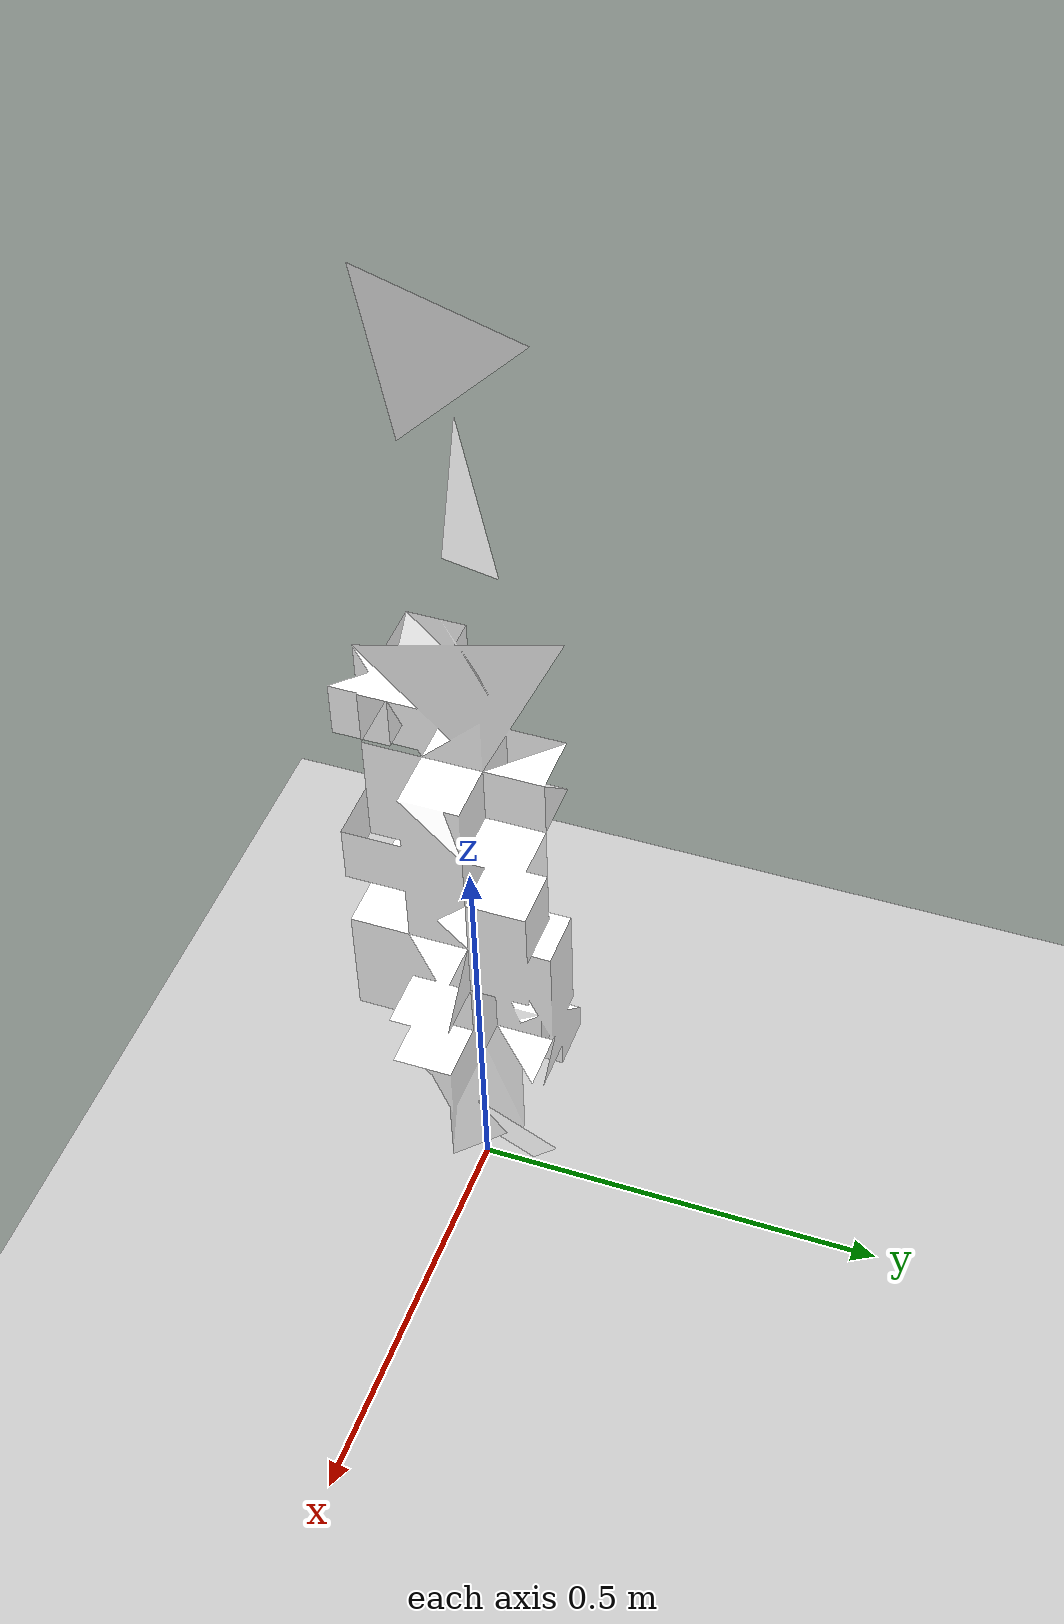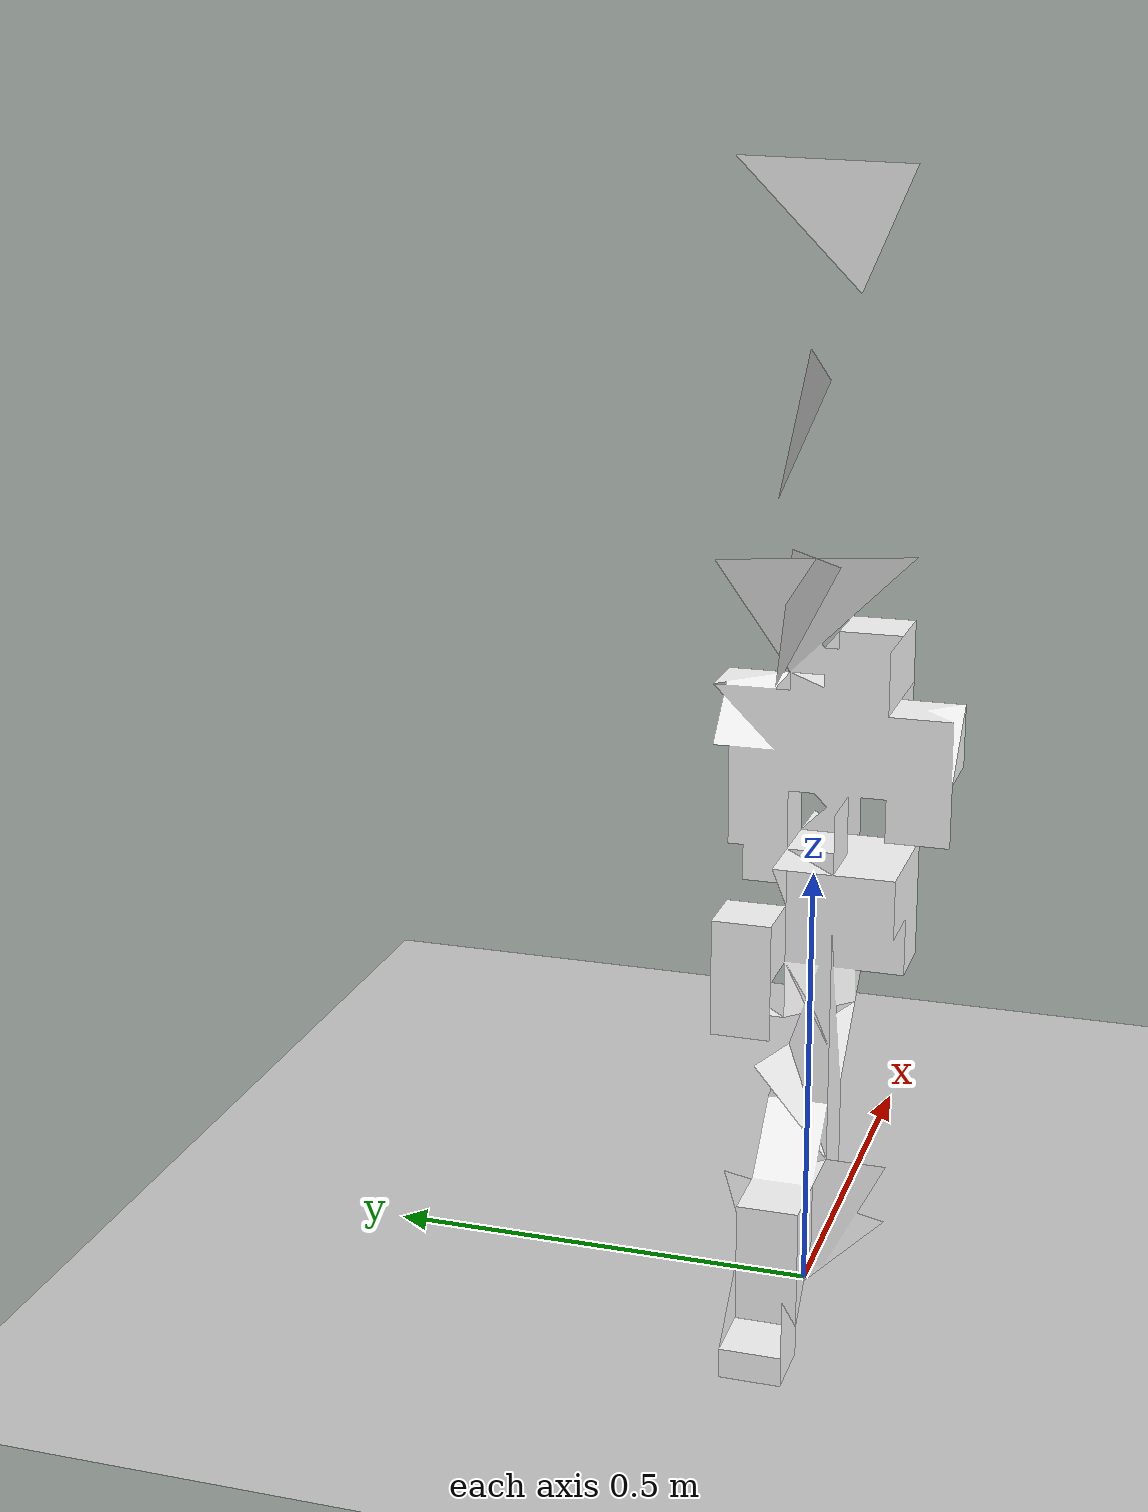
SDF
<?xml version="1.0"?>
<sdf version="1.6">
  <world name="repotest">
    <include><uri>model://sun</uri></include>
    <include><uri>model://ground_plane</uri></include>
    <include><uri>model://tomato_truss_7</uri><pose>0 0 0 0 0 0</pose></include>
    <model name="viewcam">
      <static>true</static>
      <pose>1.1 -0.9 0.9 -0 0.15 2.456</pose>
      <link name="link">
        <sensor type="camera" name="cam">
          <update_rate>10</update_rate>
          <camera><horizontal_fov>1.2</horizontal_fov><image><width>640</width><height>480</height><format>R8G8B8</format></image><clip><near>0.05</near><far>30</far></clip></camera>
          <always_on>true</always_on><visualize>false</visualize>
          <plugin name="cam_ros" filename="libgazebo_ros_camera.so"><ros><namespace>/testcam</namespace></ros></plugin>
        </sensor>
      </link>
    </model>
  </world>
</sdf>

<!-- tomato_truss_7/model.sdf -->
<sdf version="1.6">
  <model name="tomato_truss_7">
    <static>true</static>
    <link name="link">
      <collision name="collision_trunk">
        <geometry><cylinder><radius>0.012</radius><length>1.200</length></cylinder></geometry>
        <pose>0 0 0.600 0 0 0</pose>
      </collision>
      <visual name="tomato_truss_7_trunk">
        <geometry>
          <mesh>
            <uri>model://tomato_truss_7/meshes/tomato_truss_7.dae</uri>
            <submesh><name>tomato_truss_7_trunk</name></submesh>
          </mesh>
        </geometry>
        <material>
          <ambient>1 1 1 1</ambient>
          <diffuse>1 1 1 1</diffuse>
          <specular>0.1 0.1 0.1 1</specular>
          <script>
            <uri>model://tomato_truss_7/materials/scripts/</uri>
            <uri>model://tomato_truss_7/materials/textures/</uri>
            <name>branch</name>
          </script>
        </material>
      </visual>
      <visual name="tomato_truss_7_leaf0">
        <geometry>
          <mesh>
            <uri>model://tomato_truss_7/meshes/tomato_truss_7.dae</uri>
            <submesh><name>tomato_truss_7_leaf0</name></submesh>
          </mesh>
        </geometry>
        <material>
          <ambient>1 1 1 1</ambient>
          <diffuse>1 1 1 1</diffuse>
          <specular>0.1 0.1 0.1 1</specular>
          <script>
            <uri>model://tomato_truss_7/materials/scripts/</uri>
            <uri>model://tomato_truss_7/materials/textures/</uri>
            <name>branch</name>
          </script>
        </material>
      </visual>
      <visual name="tomato_truss_7_leaf1">
        <geometry>
          <mesh>
            <uri>model://tomato_truss_7/meshes/tomato_truss_7.dae</uri>
            <submesh><name>tomato_truss_7_leaf1</name></submesh>
          </mesh>
        </geometry>
        <material>
          <ambient>1 1 1 1</ambient>
          <diffuse>1 1 1 1</diffuse>
          <specular>0.1 0.1 0.1 1</specular>
          <script>
            <uri>model://tomato_truss_7/materials/scripts/</uri>
            <uri>model://tomato_truss_7/materials/textures/</uri>
            <name>branch</name>
          </script>
        </material>
      </visual>
      <visual name="tomato_truss_7_leaf2">
        <geometry>
          <mesh>
            <uri>model://tomato_truss_7/meshes/tomato_truss_7.dae</uri>
            <submesh><name>tomato_truss_7_leaf2</name></submesh>
          </mesh>
        </geometry>
        <material>
          <ambient>1 1 1 1</ambient>
          <diffuse>1 1 1 1</diffuse>
          <specular>0.1 0.1 0.1 1</specular>
          <script>
            <uri>model://tomato_truss_7/materials/scripts/</uri>
            <uri>model://tomato_truss_7/materials/textures/</uri>
            <name>branch</name>
          </script>
        </material>
      </visual>
      <visual name="tomato_truss_7_leaf3">
        <geometry>
          <mesh>
            <uri>model://tomato_truss_7/meshes/tomato_truss_7.dae</uri>
            <submesh><name>tomato_truss_7_leaf3</name></submesh>
          </mesh>
        </geometry>
        <material>
          <ambient>1 1 1 1</ambient>
          <diffuse>1 1 1 1</diffuse>
          <specular>0.1 0.1 0.1 1</specular>
          <script>
            <uri>model://tomato_truss_7/materials/scripts/</uri>
            <uri>model://tomato_truss_7/materials/textures/</uri>
            <name>branch</name>
          </script>
        </material>
      </visual>
      <visual name="tomato_truss_7_leaf4">
        <geometry>
          <mesh>
            <uri>model://tomato_truss_7/meshes/tomato_truss_7.dae</uri>
            <submesh><name>tomato_truss_7_leaf4</name></submesh>
          </mesh>
        </geometry>
        <material>
          <ambient>1 1 1 1</ambient>
          <diffuse>1 1 1 1</diffuse>
          <specular>0.1 0.1 0.1 1</specular>
          <script>
            <uri>model://tomato_truss_7/materials/scripts/</uri>
            <uri>model://tomato_truss_7/materials/textures/</uri>
            <name>branch</name>
          </script>
        </material>
      </visual>
      <visual name="tomato_truss_7_leaf5">
        <geometry>
          <mesh>
            <uri>model://tomato_truss_7/meshes/tomato_truss_7.dae</uri>
            <submesh><name>tomato_truss_7_leaf5</name></submesh>
          </mesh>
        </geometry>
        <material>
          <ambient>1 1 1 1</ambient>
          <diffuse>1 1 1 1</diffuse>
          <specular>0.1 0.1 0.1 1</specular>
          <script>
            <uri>model://tomato_truss_7/materials/scripts/</uri>
            <uri>model://tomato_truss_7/materials/textures/</uri>
            <name>branch</name>
          </script>
        </material>
      </visual>
      <visual name="tomato_truss_7_leaf6">
        <geometry>
          <mesh>
            <uri>model://tomato_truss_7/meshes/tomato_truss_7.dae</uri>
            <submesh><name>tomato_truss_7_leaf6</name></submesh>
          </mesh>
        </geometry>
        <material>
          <ambient>1 1 1 1</ambient>
          <diffuse>1 1 1 1</diffuse>
          <specular>0.1 0.1 0.1 1</specular>
          <script>
            <uri>model://tomato_truss_7/materials/scripts/</uri>
            <uri>model://tomato_truss_7/materials/textures/</uri>
            <name>branch</name>
          </script>
        </material>
      </visual>
      <visual name="tomato_truss_7_leaf7">
        <geometry>
          <mesh>
            <uri>model://tomato_truss_7/meshes/tomato_truss_7.dae</uri>
            <submesh><name>tomato_truss_7_leaf7</name></submesh>
          </mesh>
        </geometry>
        <material>
          <ambient>1 1 1 1</ambient>
          <diffuse>1 1 1 1</diffuse>
          <specular>0.1 0.1 0.1 1</specular>
          <script>
            <uri>model://tomato_truss_7/materials/scripts/</uri>
            <uri>model://tomato_truss_7/materials/textures/</uri>
            <name>branch</name>
          </script>
        </material>
      </visual>
      <visual name="tomato_truss_7_leaf8">
        <geometry>
          <mesh>
            <uri>model://tomato_truss_7/meshes/tomato_truss_7.dae</uri>
            <submesh><name>tomato_truss_7_leaf8</name></submesh>
          </mesh>
        </geometry>
        <material>
          <ambient>1 1 1 1</ambient>
          <diffuse>1 1 1 1</diffuse>
          <specular>0.1 0.1 0.1 1</specular>
          <script>
            <uri>model://tomato_truss_7/materials/scripts/</uri>
            <uri>model://tomato_truss_7/materials/textures/</uri>
            <name>branch</name>
          </script>
        </material>
      </visual>
      <visual name="tomato_truss_7_trussshot0">
        <geometry>
          <mesh>
            <uri>model://tomato_truss_7/meshes/tomato_truss_7.dae</uri>
            <submesh><name>tomato_truss_7_trussshot0</name></submesh>
          </mesh>
        </geometry>
        <material>
          <ambient>1 1 1 1</ambient>
          <diffuse>1 1 1 1</diffuse>
          <specular>0.1 0.1 0.1 1</specular>
          <script>
            <uri>model://tomato_truss_7/materials/scripts/</uri>
            <uri>model://tomato_truss_7/materials/textures/</uri>
            <name>branch</name>
          </script>
        </material>
      </visual>
      <visual name="tomato_truss_7_fruit_t0_f0">
        <geometry>
          <mesh>
            <uri>model://tomato_truss_7/meshes/tomato_truss_7.dae</uri>
            <submesh><name>tomato_truss_7_fruit_t0_f0</name></submesh>
          </mesh>
        </geometry>
        <material>
          <ambient>1 1 1 1</ambient>
          <diffuse>1 1 1 1</diffuse>
          <specular>0.1 0.1 0.1 1</specular>
          <script>
            <uri>model://tomato_truss_7/materials/scripts/</uri>
            <uri>model://tomato_truss_7/materials/textures/</uri>
            <name>fruit</name>
          </script>
        </material>
      </visual>
      <visual name="tomato_truss_7_pedicel_t0_f0">
        <geometry>
          <mesh>
            <uri>model://tomato_truss_7/meshes/tomato_truss_7.dae</uri>
            <submesh><name>tomato_truss_7_pedicel_t0_f0</name></submesh>
          </mesh>
        </geometry>
        <material>
          <ambient>1 1 1 1</ambient>
          <diffuse>1 1 1 1</diffuse>
          <specular>0.1 0.1 0.1 1</specular>
          <script>
            <uri>model://tomato_truss_7/materials/scripts/</uri>
            <uri>model://tomato_truss_7/materials/textures/</uri>
            <name>branch</name>
          </script>
        </material>
      </visual>
      <visual name="tomato_truss_7_sepal_t0_f0">
        <geometry>
          <mesh>
            <uri>model://tomato_truss_7/meshes/tomato_truss_7.dae</uri>
            <submesh><name>tomato_truss_7_sepal_t0_f0</name></submesh>
          </mesh>
        </geometry>
        <material>
          <ambient>1 1 1 1</ambient>
          <diffuse>1 1 1 1</diffuse>
          <specular>0.1 0.1 0.1 1</specular>
          <script>
            <uri>model://tomato_truss_7/materials/scripts/</uri>
            <uri>model://tomato_truss_7/materials/textures/</uri>
            <name>blossom</name>
          </script>
        </material>
      </visual>
      <visual name="tomato_truss_7_fruit_t0_f1">
        <geometry>
          <mesh>
            <uri>model://tomato_truss_7/meshes/tomato_truss_7.dae</uri>
            <submesh><name>tomato_truss_7_fruit_t0_f1</name></submesh>
          </mesh>
        </geometry>
        <material>
          <ambient>1 1 1 1</ambient>
          <diffuse>1 1 1 1</diffuse>
          <specular>0.1 0.1 0.1 1</specular>
          <script>
            <uri>model://tomato_truss_7/materials/scripts/</uri>
            <uri>model://tomato_truss_7/materials/textures/</uri>
            <name>fruit</name>
          </script>
        </material>
      </visual>
      <visual name="tomato_truss_7_pedicel_t0_f1">
        <geometry>
          <mesh>
            <uri>model://tomato_truss_7/meshes/tomato_truss_7.dae</uri>
            <submesh><name>tomato_truss_7_pedicel_t0_f1</name></submesh>
          </mesh>
        </geometry>
        <material>
          <ambient>1 1 1 1</ambient>
          <diffuse>1 1 1 1</diffuse>
          <specular>0.1 0.1 0.1 1</specular>
          <script>
            <uri>model://tomato_truss_7/materials/scripts/</uri>
            <uri>model://tomato_truss_7/materials/textures/</uri>
            <name>branch</name>
          </script>
        </material>
      </visual>
      <visual name="tomato_truss_7_sepal_t0_f1">
        <geometry>
          <mesh>
            <uri>model://tomato_truss_7/meshes/tomato_truss_7.dae</uri>
            <submesh><name>tomato_truss_7_sepal_t0_f1</name></submesh>
          </mesh>
        </geometry>
        <material>
          <ambient>1 1 1 1</ambient>
          <diffuse>1 1 1 1</diffuse>
          <specular>0.1 0.1 0.1 1</specular>
          <script>
            <uri>model://tomato_truss_7/materials/scripts/</uri>
            <uri>model://tomato_truss_7/materials/textures/</uri>
            <name>blossom</name>
          </script>
        </material>
      </visual>
      <visual name="tomato_truss_7_fruit_t0_f2">
        <geometry>
          <mesh>
            <uri>model://tomato_truss_7/meshes/tomato_truss_7.dae</uri>
            <submesh><name>tomato_truss_7_fruit_t0_f2</name></submesh>
          </mesh>
        </geometry>
        <material>
          <ambient>1 1 1 1</ambient>
          <diffuse>1 1 1 1</diffuse>
          <specular>0.1 0.1 0.1 1</specular>
          <script>
            <uri>model://tomato_truss_7/materials/scripts/</uri>
            <uri>model://tomato_truss_7/materials/textures/</uri>
            <name>fruit</name>
          </script>
        </material>
      </visual>
      <visual name="tomato_truss_7_pedicel_t0_f2">
        <geometry>
          <mesh>
            <uri>model://tomato_truss_7/meshes/tomato_truss_7.dae</uri>
            <submesh><name>tomato_truss_7_pedicel_t0_f2</name></submesh>
          </mesh>
        </geometry>
        <material>
          <ambient>1 1 1 1</ambient>
          <diffuse>1 1 1 1</diffuse>
          <specular>0.1 0.1 0.1 1</specular>
          <script>
            <uri>model://tomato_truss_7/materials/scripts/</uri>
            <uri>model://tomato_truss_7/materials/textures/</uri>
            <name>branch</name>
          </script>
        </material>
      </visual>
      <visual name="tomato_truss_7_sepal_t0_f2">
        <geometry>
          <mesh>
            <uri>model://tomato_truss_7/meshes/tomato_truss_7.dae</uri>
            <submesh><name>tomato_truss_7_sepal_t0_f2</name></submesh>
          </mesh>
        </geometry>
        <material>
          <ambient>1 1 1 1</ambient>
          <diffuse>1 1 1 1</diffuse>
          <specular>0.1 0.1 0.1 1</specular>
          <script>
            <uri>model://tomato_truss_7/materials/scripts/</uri>
            <uri>model://tomato_truss_7/materials/textures/</uri>
            <name>blossom</name>
          </script>
        </material>
      </visual>
      <visual name="tomato_truss_7_fruit_t0_f3">
        <geometry>
          <mesh>
            <uri>model://tomato_truss_7/meshes/tomato_truss_7.dae</uri>
            <submesh><name>tomato_truss_7_fruit_t0_f3</name></submesh>
          </mesh>
        </geometry>
        <material>
          <ambient>1 1 1 1</ambient>
          <diffuse>1 1 1 1</diffuse>
          <specular>0.1 0.1 0.1 1</specular>
          <script>
            <uri>model://tomato_truss_7/materials/scripts/</uri>
            <uri>model://tomato_truss_7/materials/textures/</uri>
            <name>fruit</name>
          </script>
        </material>
      </visual>
      <visual name="tomato_truss_7_pedicel_t0_f3">
        <geometry>
          <mesh>
            <uri>model://tomato_truss_7/meshes/tomato_truss_7.dae</uri>
            <submesh><name>tomato_truss_7_pedicel_t0_f3</name></submesh>
          </mesh>
        </geometry>
        <material>
          <ambient>1 1 1 1</ambient>
          <diffuse>1 1 1 1</diffuse>
          <specular>0.1 0.1 0.1 1</specular>
          <script>
            <uri>model://tomato_truss_7/materials/scripts/</uri>
            <uri>model://tomato_truss_7/materials/textures/</uri>
            <name>branch</name>
          </script>
        </material>
      </visual>
      <visual name="tomato_truss_7_sepal_t0_f3">
        <geometry>
          <mesh>
            <uri>model://tomato_truss_7/meshes/tomato_truss_7.dae</uri>
            <submesh><name>tomato_truss_7_sepal_t0_f3</name></submesh>
          </mesh>
        </geometry>
        <material>
          <ambient>1 1 1 1</ambient>
          <diffuse>1 1 1 1</diffuse>
          <specular>0.1 0.1 0.1 1</specular>
          <script>
            <uri>model://tomato_truss_7/materials/scripts/</uri>
            <uri>model://tomato_truss_7/materials/textures/</uri>
            <name>blossom</name>
          </script>
        </material>
      </visual>
      <visual name="tomato_truss_7_fruit_t0_f4">
        <geometry>
          <mesh>
            <uri>model://tomato_truss_7/meshes/tomato_truss_7.dae</uri>
            <submesh><name>tomato_truss_7_fruit_t0_f4</name></submesh>
          </mesh>
        </geometry>
        <material>
          <ambient>1 1 1 1</ambient>
          <diffuse>1 1 1 1</diffuse>
          <specular>0.1 0.1 0.1 1</specular>
          <script>
            <uri>model://tomato_truss_7/materials/scripts/</uri>
            <uri>model://tomato_truss_7/materials/textures/</uri>
            <name>fruit</name>
          </script>
        </material>
      </visual>
      <visual name="tomato_truss_7_pedicel_t0_f4">
        <geometry>
          <mesh>
            <uri>model://tomato_truss_7/meshes/tomato_truss_7.dae</uri>
            <submesh><name>tomato_truss_7_pedicel_t0_f4</name></submesh>
          </mesh>
        </geometry>
        <material>
          <ambient>1 1 1 1</ambient>
          <diffuse>1 1 1 1</diffuse>
          <specular>0.1 0.1 0.1 1</specular>
          <script>
            <uri>model://tomato_truss_7/materials/scripts/</uri>
            <uri>model://tomato_truss_7/materials/textures/</uri>
            <name>branch</name>
          </script>
        </material>
      </visual>
      <visual name="tomato_truss_7_sepal_t0_f4">
        <geometry>
          <mesh>
            <uri>model://tomato_truss_7/meshes/tomato_truss_7.dae</uri>
            <submesh><name>tomato_truss_7_sepal_t0_f4</name></submesh>
          </mesh>
        </geometry>
        <material>
          <ambient>1 1 1 1</ambient>
          <diffuse>1 1 1 1</diffuse>
          <specular>0.1 0.1 0.1 1</specular>
          <script>
            <uri>model://tomato_truss_7/materials/scripts/</uri>
            <uri>model://tomato_truss_7/materials/textures/</uri>
            <name>blossom</name>
          </script>
        </material>
      </visual>
      <visual name="tomato_truss_7_fruit_t0_f5">
        <geometry>
          <mesh>
            <uri>model://tomato_truss_7/meshes/tomato_truss_7.dae</uri>
            <submesh><name>tomato_truss_7_fruit_t0_f5</name></submesh>
          </mesh>
        </geometry>
        <material>
          <ambient>1 1 1 1</ambient>
          <diffuse>1 1 1 1</diffuse>
          <specular>0.1 0.1 0.1 1</specular>
          <script>
            <uri>model://tomato_truss_7/materials/scripts/</uri>
            <uri>model://tomato_truss_7/materials/textures/</uri>
            <name>fruit</name>
          </script>
        </material>
      </visual>
      <visual name="tomato_truss_7_pedicel_t0_f5">
        <geometry>
          <mesh>
            <uri>model://tomato_truss_7/meshes/tomato_truss_7.dae</uri>
            <submesh><name>tomato_truss_7_pedicel_t0_f5</name></submesh>
          </mesh>
        </geometry>
        <material>
          <ambient>1 1 1 1</ambient>
          <diffuse>1 1 1 1</diffuse>
          <specular>0.1 0.1 0.1 1</specular>
          <script>
            <uri>model://tomato_truss_7/materials/scripts/</uri>
            <uri>model://tomato_truss_7/materials/textures/</uri>
            <name>branch</name>
          </script>
        </material>
      </visual>
      <visual name="tomato_truss_7_sepal_t0_f5">
        <geometry>
          <mesh>
            <uri>model://tomato_truss_7/meshes/tomato_truss_7.dae</uri>
            <submesh><name>tomato_truss_7_sepal_t0_f5</name></submesh>
          </mesh>
        </geometry>
        <material>
          <ambient>1 1 1 1</ambient>
          <diffuse>1 1 1 1</diffuse>
          <specular>0.1 0.1 0.1 1</specular>
          <script>
            <uri>model://tomato_truss_7/materials/scripts/</uri>
            <uri>model://tomato_truss_7/materials/textures/</uri>
            <name>blossom</name>
          </script>
        </material>
      </visual>
      <visual name="tomato_truss_7_fruit_t0_f6">
        <geometry>
          <mesh>
            <uri>model://tomato_truss_7/meshes/tomato_truss_7.dae</uri>
            <submesh><name>tomato_truss_7_fruit_t0_f6</name></submesh>
          </mesh>
        </geometry>
        <material>
          <ambient>1 1 1 1</ambient>
          <diffuse>1 1 1 1</diffuse>
          <specular>0.1 0.1 0.1 1</specular>
          <script>
            <uri>model://tomato_truss_7/materials/scripts/</uri>
            <uri>model://tomato_truss_7/materials/textures/</uri>
            <name>fruit</name>
          </script>
        </material>
      </visual>
      <visual name="tomato_truss_7_pedicel_t0_f6">
        <geometry>
          <mesh>
            <uri>model://tomato_truss_7/meshes/tomato_truss_7.dae</uri>
            <submesh><name>tomato_truss_7_pedicel_t0_f6</name></submesh>
          </mesh>
        </geometry>
        <material>
          <ambient>1 1 1 1</ambient>
          <diffuse>1 1 1 1</diffuse>
          <specular>0.1 0.1 0.1 1</specular>
          <script>
            <uri>model://tomato_truss_7/materials/scripts/</uri>
            <uri>model://tomato_truss_7/materials/textures/</uri>
            <name>branch</name>
          </script>
        </material>
      </visual>
      <visual name="tomato_truss_7_sepal_t0_f6">
        <geometry>
          <mesh>
            <uri>model://tomato_truss_7/meshes/tomato_truss_7.dae</uri>
            <submesh><name>tomato_truss_7_sepal_t0_f6</name></submesh>
          </mesh>
        </geometry>
        <material>
          <ambient>1 1 1 1</ambient>
          <diffuse>1 1 1 1</diffuse>
          <specular>0.1 0.1 0.1 1</specular>
          <script>
            <uri>model://tomato_truss_7/materials/scripts/</uri>
            <uri>model://tomato_truss_7/materials/textures/</uri>
            <name>blossom</name>
          </script>
        </material>
      </visual>
      <visual name="tomato_truss_7_fruit_t0_f7">
        <geometry>
          <mesh>
            <uri>model://tomato_truss_7/meshes/tomato_truss_7.dae</uri>
            <submesh><name>tomato_truss_7_fruit_t0_f7</name></submesh>
          </mesh>
        </geometry>
        <material>
          <ambient>1 1 1 1</ambient>
          <diffuse>1 1 1 1</diffuse>
          <specular>0.1 0.1 0.1 1</specular>
          <script>
            <uri>model://tomato_truss_7/materials/scripts/</uri>
            <uri>model://tomato_truss_7/materials/textures/</uri>
            <name>fruit</name>
          </script>
        </material>
      </visual>
      <visual name="tomato_truss_7_pedicel_t0_f7">
        <geometry>
          <mesh>
            <uri>model://tomato_truss_7/meshes/tomato_truss_7.dae</uri>
            <submesh><name>tomato_truss_7_pedicel_t0_f7</name></submesh>
          </mesh>
        </geometry>
        <material>
          <ambient>1 1 1 1</ambient>
          <diffuse>1 1 1 1</diffuse>
          <specular>0.1 0.1 0.1 1</specular>
          <script>
            <uri>model://tomato_truss_7/materials/scripts/</uri>
            <uri>model://tomato_truss_7/materials/textures/</uri>
            <name>branch</name>
          </script>
        </material>
      </visual>
      <visual name="tomato_truss_7_sepal_t0_f7">
        <geometry>
          <mesh>
            <uri>model://tomato_truss_7/meshes/tomato_truss_7.dae</uri>
            <submesh><name>tomato_truss_7_sepal_t0_f7</name></submesh>
          </mesh>
        </geometry>
        <material>
          <ambient>1 1 1 1</ambient>
          <diffuse>1 1 1 1</diffuse>
          <specular>0.1 0.1 0.1 1</specular>
          <script>
            <uri>model://tomato_truss_7/materials/scripts/</uri>
            <uri>model://tomato_truss_7/materials/textures/</uri>
            <name>blossom</name>
          </script>
        </material>
      </visual>
      <visual name="tomato_truss_7_trussshot1">
        <geometry>
          <mesh>
            <uri>model://tomato_truss_7/meshes/tomato_truss_7.dae</uri>
            <submesh><name>tomato_truss_7_trussshot1</name></submesh>
          </mesh>
        </geometry>
        <material>
          <ambient>1 1 1 1</ambient>
          <diffuse>1 1 1 1</diffuse>
          <specular>0.1 0.1 0.1 1</specular>
          <script>
            <uri>model://tomato_truss_7/materials/scripts/</uri>
            <uri>model://tomato_truss_7/materials/textures/</uri>
            <name>branch</name>
          </script>
        </material>
      </visual>
      <visual name="tomato_truss_7_fruit_t1_f0">
        <geometry>
          <mesh>
            <uri>model://tomato_truss_7/meshes/tomato_truss_7.dae</uri>
            <submesh><name>tomato_truss_7_fruit_t1_f0</name></submesh>
          </mesh>
        </geometry>
        <material>
          <ambient>1 1 1 1</ambient>
          <diffuse>1 1 1 1</diffuse>
          <specular>0.1 0.1 0.1 1</specular>
          <script>
            <uri>model://tomato_truss_7/materials/scripts/</uri>
            <uri>model://tomato_truss_7/materials/textures/</uri>
            <name>fruit</name>
          </script>
        </material>
      </visual>
      <visual name="tomato_truss_7_pedicel_t1_f0">
        <geometry>
          <mesh>
            <uri>model://tomato_truss_7/meshes/tomato_truss_7.dae</uri>
            <submesh><name>tomato_truss_7_pedicel_t1_f0</name></submesh>
          </mesh>
        </geometry>
        <material>
          <ambient>1 1 1 1</ambient>
          <diffuse>1 1 1 1</diffuse>
          <specular>0.1 0.1 0.1 1</specular>
          <script>
            <uri>model://tomato_truss_7/materials/scripts/</uri>
            <uri>model://tomato_truss_7/materials/textures/</uri>
            <name>branch</name>
          </script>
        </material>
      </visual>
      <visual name="tomato_truss_7_sepal_t1_f0">
        <geometry>
          <mesh>
            <uri>model://tomato_truss_7/meshes/tomato_truss_7.dae</uri>
            <submesh><name>tomato_truss_7_sepal_t1_f0</name></submesh>
          </mesh>
        </geometry>
        <material>
          <ambient>1 1 1 1</ambient>
          <diffuse>1 1 1 1</diffuse>
          <specular>0.1 0.1 0.1 1</specular>
          <script>
            <uri>model://tomato_truss_7/materials/scripts/</uri>
            <uri>model://tomato_truss_7/materials/textures/</uri>
            <name>blossom</name>
          </script>
        </material>
      </visual>
      <visual name="tomato_truss_7_fruit_t1_f1">
        <geometry>
          <mesh>
            <uri>model://tomato_truss_7/meshes/tomato_truss_7.dae</uri>
            <submesh><name>tomato_truss_7_fruit_t1_f1</name></submesh>
          </mesh>
        </geometry>
        <material>
          <ambient>1 1 1 1</ambient>
          <diffuse>1 1 1 1</diffuse>
          <specular>0.1 0.1 0.1 1</specular>
          <script>
            <uri>model://tomato_truss_7/materials/scripts/</uri>
            <uri>model://tomato_truss_7/materials/textures/</uri>
            <name>fruit</name>
          </script>
        </material>
      </visual>
      <visual name="tomato_truss_7_pedicel_t1_f1">
        <geometry>
          <mesh>
            <uri>model://tomato_truss_7/meshes/tomato_truss_7.dae</uri>
            <submesh><name>tomato_truss_7_pedicel_t1_f1</name></submesh>
          </mesh>
        </geometry>
        <material>
          <ambient>1 1 1 1</ambient>
          <diffuse>1 1 1 1</diffuse>
          <specular>0.1 0.1 0.1 1</specular>
          <script>
            <uri>model://tomato_truss_7/materials/scripts/</uri>
            <uri>model://tomato_truss_7/materials/textures/</uri>
            <name>branch</name>
          </script>
        </material>
      </visual>
      <visual name="tomato_truss_7_sepal_t1_f1">
        <geometry>
          <mesh>
            <uri>model://tomato_truss_7/meshes/tomato_truss_7.dae</uri>
            <submesh><name>tomato_truss_7_sepal_t1_f1</name></submesh>
          </mesh>
        </geometry>
        <material>
          <ambient>1 1 1 1</ambient>
          <diffuse>1 1 1 1</diffuse>
          <specular>0.1 0.1 0.1 1</specular>
          <script>
            <uri>model://tomato_truss_7/materials/scripts/</uri>
            <uri>model://tomato_truss_7/materials/textures/</uri>
            <name>blossom</name>
          </script>
        </material>
      </visual>
      <visual name="tomato_truss_7_fruit_t1_f2">
        <geometry>
          <mesh>
            <uri>model://tomato_truss_7/meshes/tomato_truss_7.dae</uri>
            <submesh><name>tomato_truss_7_fruit_t1_f2</name></submesh>
          </mesh>
        </geometry>
        <material>
          <ambient>1 1 1 1</ambient>
          <diffuse>1 1 1 1</diffuse>
          <specular>0.1 0.1 0.1 1</specular>
          <script>
            <uri>model://tomato_truss_7/materials/scripts/</uri>
            <uri>model://tomato_truss_7/materials/textures/</uri>
            <name>fruit</name>
          </script>
        </material>
      </visual>
      <visual name="tomato_truss_7_pedicel_t1_f2">
        <geometry>
          <mesh>
            <uri>model://tomato_truss_7/meshes/tomato_truss_7.dae</uri>
            <submesh><name>tomato_truss_7_pedicel_t1_f2</name></submesh>
          </mesh>
        </geometry>
        <material>
          <ambient>1 1 1 1</ambient>
          <diffuse>1 1 1 1</diffuse>
          <specular>0.1 0.1 0.1 1</specular>
          <script>
            <uri>model://tomato_truss_7/materials/scripts/</uri>
            <uri>model://tomato_truss_7/materials/textures/</uri>
            <name>branch</name>
          </script>
        </material>
      </visual>
      <visual name="tomato_truss_7_sepal_t1_f2">
        <geometry>
          <mesh>
            <uri>model://tomato_truss_7/meshes/tomato_truss_7.dae</uri>
            <submesh><name>tomato_truss_7_sepal_t1_f2</name></submesh>
          </mesh>
        </geometry>
        <material>
          <ambient>1 1 1 1</ambient>
          <diffuse>1 1 1 1</diffuse>
          <specular>0.1 0.1 0.1 1</specular>
          <script>
            <uri>model://tomato_truss_7/materials/scripts/</uri>
            <uri>model://tomato_truss_7/materials/textures/</uri>
            <name>blossom</name>
          </script>
        </material>
      </visual>
      <visual name="tomato_truss_7_fruit_t1_f3">
        <geometry>
          <mesh>
            <uri>model://tomato_truss_7/meshes/tomato_truss_7.dae</uri>
            <submesh><name>tomato_truss_7_fruit_t1_f3</name></submesh>
          </mesh>
        </geometry>
        <material>
          <ambient>1 1 1 1</ambient>
          <diffuse>1 1 1 1</diffuse>
          <specular>0.1 0.1 0.1 1</specular>
          <script>
            <uri>model://tomato_truss_7/materials/scripts/</uri>
            <uri>model://tomato_truss_7/materials/textures/</uri>
            <name>fruit</name>
          </script>
        </material>
      </visual>
      <visual name="tomato_truss_7_pedicel_t1_f3">
        <geometry>
          <mesh>
            <uri>model://tomato_truss_7/meshes/tomato_truss_7.dae</uri>
            <submesh><name>tomato_truss_7_pedicel_t1_f3</name></submesh>
          </mesh>
        </geometry>
        <material>
          <ambient>1 1 1 1</ambient>
          <diffuse>1 1 1 1</diffuse>
          <specular>0.1 0.1 0.1 1</specular>
          <script>
            <uri>model://tomato_truss_7/materials/scripts/</uri>
            <uri>model://tomato_truss_7/materials/textures/</uri>
            <name>branch</name>
          </script>
        </material>
      </visual>
      <visual name="tomato_truss_7_sepal_t1_f3">
        <geometry>
          <mesh>
            <uri>model://tomato_truss_7/meshes/tomato_truss_7.dae</uri>
            <submesh><name>tomato_truss_7_sepal_t1_f3</name></submesh>
          </mesh>
        </geometry>
        <material>
          <ambient>1 1 1 1</ambient>
          <diffuse>1 1 1 1</diffuse>
          <specular>0.1 0.1 0.1 1</specular>
          <script>
            <uri>model://tomato_truss_7/materials/scripts/</uri>
            <uri>model://tomato_truss_7/materials/textures/</uri>
            <name>blossom</name>
          </script>
        </material>
      </visual>
      <visual name="tomato_truss_7_fruit_t1_f4">
        <geometry>
          <mesh>
            <uri>model://tomato_truss_7/meshes/tomato_truss_7.dae</uri>
            <submesh><name>tomato_truss_7_fruit_t1_f4</name></submesh>
          </mesh>
        </geometry>
        <material>
          <ambient>1 1 1 1</ambient>
          <diffuse>1 1 1 1</diffuse>
          <specular>0.1 0.1 0.1 1</specular>
          <script>
            <uri>model://tomato_truss_7/materials/scripts/</uri>
            <uri>model://tomato_truss_7/materials/textures/</uri>
            <name>fruit</name>
          </script>
        </material>
      </visual>
      <visual name="tomato_truss_7_pedicel_t1_f4">
        <geometry>
          <mesh>
            <uri>model://tomato_truss_7/meshes/tomato_truss_7.dae</uri>
            <submesh><name>tomato_truss_7_pedicel_t1_f4</name></submesh>
          </mesh>
        </geometry>
        <material>
          <ambient>1 1 1 1</ambient>
          <diffuse>1 1 1 1</diffuse>
          <specular>0.1 0.1 0.1 1</specular>
          <script>
            <uri>model://tomato_truss_7/materials/scripts/</uri>
            <uri>model://tomato_truss_7/materials/textures/</uri>
            <name>branch</name>
          </script>
        </material>
      </visual>
      <visual name="tomato_truss_7_sepal_t1_f4">
        <geometry>
          <mesh>
            <uri>model://tomato_truss_7/meshes/tomato_truss_7.dae</uri>
            <submesh><name>tomato_truss_7_sepal_t1_f4</name></submesh>
          </mesh>
        </geometry>
        <material>
          <ambient>1 1 1 1</ambient>
          <diffuse>1 1 1 1</diffuse>
          <specular>0.1 0.1 0.1 1</specular>
          <script>
            <uri>model://tomato_truss_7/materials/scripts/</uri>
            <uri>model://tomato_truss_7/materials/textures/</uri>
            <name>blossom</name>
          </script>
        </material>
      </visual>
      <visual name="tomato_truss_7_trussshot2">
        <geometry>
          <mesh>
            <uri>model://tomato_truss_7/meshes/tomato_truss_7.dae</uri>
            <submesh><name>tomato_truss_7_trussshot2</name></submesh>
          </mesh>
        </geometry>
        <material>
          <ambient>1 1 1 1</ambient>
          <diffuse>1 1 1 1</diffuse>
          <specular>0.1 0.1 0.1 1</specular>
          <script>
            <uri>model://tomato_truss_7/materials/scripts/</uri>
            <uri>model://tomato_truss_7/materials/textures/</uri>
            <name>branch</name>
          </script>
        </material>
      </visual>
      <visual name="tomato_truss_7_fruit_t2_f0">
        <geometry>
          <mesh>
            <uri>model://tomato_truss_7/meshes/tomato_truss_7.dae</uri>
            <submesh><name>tomato_truss_7_fruit_t2_f0</name></submesh>
          </mesh>
        </geometry>
        <material>
          <ambient>1 1 1 1</ambient>
          <diffuse>1 1 1 1</diffuse>
          <specular>0.1 0.1 0.1 1</specular>
          <script>
            <uri>model://tomato_truss_7/materials/scripts/</uri>
            <uri>model://tomato_truss_7/materials/textures/</uri>
            <name>fruit</name>
          </script>
        </material>
      </visual>
      <visual name="tomato_truss_7_pedicel_t2_f0">
        <geometry>
          <mesh>
            <uri>model://tomato_truss_7/meshes/tomato_truss_7.dae</uri>
            <submesh><name>tomato_truss_7_pedicel_t2_f0</name></submesh>
          </mesh>
        </geometry>
        <material>
          <ambient>1 1 1 1</ambient>
          <diffuse>1 1 1 1</diffuse>
          <specular>0.1 0.1 0.1 1</specular>
          <script>
            <uri>model://tomato_truss_7/materials/scripts/</uri>
            <uri>model://tomato_truss_7/materials/textures/</uri>
            <name>branch</name>
          </script>
        </material>
      </visual>
      <visual name="tomato_truss_7_sepal_t2_f0">
        <geometry>
          <mesh>
            <uri>model://tomato_truss_7/meshes/tomato_truss_7.dae</uri>
            <submesh><name>tomato_truss_7_sepal_t2_f0</name></submesh>
          </mesh>
        </geometry>
        <material>
          <ambient>1 1 1 1</ambient>
          <diffuse>1 1 1 1</diffuse>
          <specular>0.1 0.1 0.1 1</specular>
          <script>
            <uri>model://tomato_truss_7/materials/scripts/</uri>
            <uri>model://tomato_truss_7/materials/textures/</uri>
            <name>blossom</name>
          </script>
        </material>
      </visual>
      <visual name="tomato_truss_7_fruit_t2_f1">
        <geometry>
          <mesh>
            <uri>model://tomato_truss_7/meshes/tomato_truss_7.dae</uri>
            <submesh><name>tomato_truss_7_fruit_t2_f1</name></submesh>
          </mesh>
        </geometry>
        <material>
          <ambient>1 1 1 1</ambient>
          <diffuse>1 1 1 1</diffuse>
          <specular>0.1 0.1 0.1 1</specular>
          <script>
            <uri>model://tomato_truss_7/materials/scripts/</uri>
            <uri>model://tomato_truss_7/materials/textures/</uri>
            <name>fruit</name>
          </script>
        </material>
      </visual>
      <visual name="tomato_truss_7_pedicel_t2_f1">
        <geometry>
          <mesh>
            <uri>model://tomato_truss_7/meshes/tomato_truss_7.dae</uri>
            <submesh><name>tomato_truss_7_pedicel_t2_f1</name></submesh>
          </mesh>
        </geometry>
        <material>
          <ambient>1 1 1 1</ambient>
          <diffuse>1 1 1 1</diffuse>
          <specular>0.1 0.1 0.1 1</specular>
          <script>
            <uri>model://tomato_truss_7/materials/scripts/</uri>
            <uri>model://tomato_truss_7/materials/textures/</uri>
            <name>branch</name>
          </script>
        </material>
      </visual>
      <visual name="tomato_truss_7_sepal_t2_f1">
        <geometry>
          <mesh>
            <uri>model://tomato_truss_7/meshes/tomato_truss_7.dae</uri>
            <submesh><name>tomato_truss_7_sepal_t2_f1</name></submesh>
          </mesh>
        </geometry>
        <material>
          <ambient>1 1 1 1</ambient>
          <diffuse>1 1 1 1</diffuse>
          <specular>0.1 0.1 0.1 1</specular>
          <script>
            <uri>model://tomato_truss_7/materials/scripts/</uri>
            <uri>model://tomato_truss_7/materials/textures/</uri>
            <name>blossom</name>
          </script>
        </material>
      </visual>
      <visual name="tomato_truss_7_fruit_t2_f2">
        <geometry>
          <mesh>
            <uri>model://tomato_truss_7/meshes/tomato_truss_7.dae</uri>
            <submesh><name>tomato_truss_7_fruit_t2_f2</name></submesh>
          </mesh>
        </geometry>
        <material>
          <ambient>1 1 1 1</ambient>
          <diffuse>1 1 1 1</diffuse>
          <specular>0.1 0.1 0.1 1</specular>
          <script>
            <uri>model://tomato_truss_7/materials/scripts/</uri>
            <uri>model://tomato_truss_7/materials/textures/</uri>
            <name>fruit</name>
          </script>
        </material>
      </visual>
      <visual name="tomato_truss_7_pedicel_t2_f2">
        <geometry>
          <mesh>
            <uri>model://tomato_truss_7/meshes/tomato_truss_7.dae</uri>
            <submesh><name>tomato_truss_7_pedicel_t2_f2</name></submesh>
          </mesh>
        </geometry>
        <material>
          <ambient>1 1 1 1</ambient>
          <diffuse>1 1 1 1</diffuse>
          <specular>0.1 0.1 0.1 1</specular>
          <script>
            <uri>model://tomato_truss_7/materials/scripts/</uri>
            <uri>model://tomato_truss_7/materials/textures/</uri>
            <name>branch</name>
          </script>
        </material>
      </visual>
      <visual name="tomato_truss_7_sepal_t2_f2">
        <geometry>
          <mesh>
            <uri>model://tomato_truss_7/meshes/tomato_truss_7.dae</uri>
            <submesh><name>tomato_truss_7_sepal_t2_f2</name></submesh>
          </mesh>
        </geometry>
        <material>
          <ambient>1 1 1 1</ambient>
          <diffuse>1 1 1 1</diffuse>
          <specular>0.1 0.1 0.1 1</specular>
          <script>
            <uri>model://tomato_truss_7/materials/scripts/</uri>
            <uri>model://tomato_truss_7/materials/textures/</uri>
            <name>blossom</name>
          </script>
        </material>
      </visual>
      <visual name="tomato_truss_7_fruit_t2_f3">
        <geometry>
          <mesh>
            <uri>model://tomato_truss_7/meshes/tomato_truss_7.dae</uri>
            <submesh><name>tomato_truss_7_fruit_t2_f3</name></submesh>
          </mesh>
        </geometry>
        <material>
          <ambient>1 1 1 1</ambient>
          <diffuse>1 1 1 1</diffuse>
          <specular>0.1 0.1 0.1 1</specular>
          <script>
            <uri>model://tomato_truss_7/materials/scripts/</uri>
            <uri>model://tomato_truss_7/materials/textures/</uri>
            <name>fruit</name>
          </script>
        </material>
      </visual>
      <visual name="tomato_truss_7_pedicel_t2_f3">
        <geometry>
          <mesh>
            <uri>model://tomato_truss_7/meshes/tomato_truss_7.dae</uri>
            <submesh><name>tomato_truss_7_pedicel_t2_f3</name></submesh>
          </mesh>
        </geometry>
        <material>
          <ambient>1 1 1 1</ambient>
          <diffuse>1 1 1 1</diffuse>
          <specular>0.1 0.1 0.1 1</specular>
          <script>
            <uri>model://tomato_truss_7/materials/scripts/</uri>
            <uri>model://tomato_truss_7/materials/textures/</uri>
            <name>branch</name>
          </script>
        </material>
      </visual>
      <visual name="tomato_truss_7_sepal_t2_f3">
        <geometry>
          <mesh>
            <uri>model://tomato_truss_7/meshes/tomato_truss_7.dae</uri>
            <submesh><name>tomato_truss_7_sepal_t2_f3</name></submesh>
          </mesh>
        </geometry>
        <material>
          <ambient>1 1 1 1</ambient>
          <diffuse>1 1 1 1</diffuse>
          <specular>0.1 0.1 0.1 1</specular>
          <script>
            <uri>model://tomato_truss_7/materials/scripts/</uri>
            <uri>model://tomato_truss_7/materials/textures/</uri>
            <name>blossom</name>
          </script>
        </material>
      </visual>
      <visual name="tomato_truss_7_fruit_t2_f4">
        <geometry>
          <mesh>
            <uri>model://tomato_truss_7/meshes/tomato_truss_7.dae</uri>
            <submesh><name>tomato_truss_7_fruit_t2_f4</name></submesh>
          </mesh>
        </geometry>
        <material>
          <ambient>1 1 1 1</ambient>
          <diffuse>1 1 1 1</diffuse>
          <specular>0.1 0.1 0.1 1</specular>
          <script>
            <uri>model://tomato_truss_7/materials/scripts/</uri>
            <uri>model://tomato_truss_7/materials/textures/</uri>
            <name>fruit</name>
          </script>
        </material>
      </visual>
      <visual name="tomato_truss_7_pedicel_t2_f4">
        <geometry>
          <mesh>
            <uri>model://tomato_truss_7/meshes/tomato_truss_7.dae</uri>
            <submesh><name>tomato_truss_7_pedicel_t2_f4</name></submesh>
          </mesh>
        </geometry>
        <material>
          <ambient>1 1 1 1</ambient>
          <diffuse>1 1 1 1</diffuse>
          <specular>0.1 0.1 0.1 1</specular>
          <script>
            <uri>model://tomato_truss_7/materials/scripts/</uri>
            <uri>model://tomato_truss_7/materials/textures/</uri>
            <name>branch</name>
          </script>
        </material>
      </visual>
      <visual name="tomato_truss_7_sepal_t2_f4">
        <geometry>
          <mesh>
            <uri>model://tomato_truss_7/meshes/tomato_truss_7.dae</uri>
            <submesh><name>tomato_truss_7_sepal_t2_f4</name></submesh>
          </mesh>
        </geometry>
        <material>
          <ambient>1 1 1 1</ambient>
          <diffuse>1 1 1 1</diffuse>
          <specular>0.1 0.1 0.1 1</specular>
          <script>
            <uri>model://tomato_truss_7/materials/scripts/</uri>
            <uri>model://tomato_truss_7/materials/textures/</uri>
            <name>blossom</name>
          </script>
        </material>
      </visual>
      <visual name="tomato_truss_7_trussshot3">
        <geometry>
          <mesh>
            <uri>model://tomato_truss_7/meshes/tomato_truss_7.dae</uri>
            <submesh><name>tomato_truss_7_trussshot3</name></submesh>
          </mesh>
        </geometry>
        <material>
          <ambient>1 1 1 1</ambient>
          <diffuse>1 1 1 1</diffuse>
          <specular>0.1 0.1 0.1 1</specular>
          <script>
            <uri>model://tomato_truss_7/materials/scripts/</uri>
            <uri>model://tomato_truss_7/materials/textures/</uri>
            <name>branch</name>
          </script>
        </material>
      </visual>
      <visual name="tomato_truss_7_fruit_t3_f0">
        <geometry>
          <mesh>
            <uri>model://tomato_truss_7/meshes/tomato_truss_7.dae</uri>
            <submesh><name>tomato_truss_7_fruit_t3_f0</name></submesh>
          </mesh>
        </geometry>
        <material>
          <ambient>1 1 1 1</ambient>
          <diffuse>1 1 1 1</diffuse>
          <specular>0.1 0.1 0.1 1</specular>
          <script>
            <uri>model://tomato_truss_7/materials/scripts/</uri>
            <uri>model://tomato_truss_7/materials/textures/</uri>
            <name>fruit</name>
          </script>
        </material>
      </visual>
      <visual name="tomato_truss_7_pedicel_t3_f0">
        <geometry>
          <mesh>
            <uri>model://tomato_truss_7/meshes/tomato_truss_7.dae</uri>
            <submesh><name>tomato_truss_7_pedicel_t3_f0</name></submesh>
          </mesh>
        </geometry>
        <material>
          <ambient>1 1 1 1</ambient>
          <diffuse>1 1 1 1</diffuse>
          <specular>0.1 0.1 0.1 1</specular>
          <script>
            <uri>model://tomato_truss_7/materials/scripts/</uri>
            <uri>model://tomato_truss_7/materials/textures/</uri>
            <name>branch</name>
          </script>
        </material>
      </visual>
      <visual name="tomato_truss_7_sepal_t3_f0">
        <geometry>
          <mesh>
            <uri>model://tomato_truss_7/meshes/tomato_truss_7.dae</uri>
            <submesh><name>tomato_truss_7_sepal_t3_f0</name></submesh>
          </mesh>
        </geometry>
        <material>
          <ambient>1 1 1 1</ambient>
          <diffuse>1 1 1 1</diffuse>
          <specular>0.1 0.1 0.1 1</specular>
          <script>
            <uri>model://tomato_truss_7/materials/scripts/</uri>
            <uri>model://tomato_truss_7/materials/textures/</uri>
            <name>blossom</name>
          </script>
        </material>
      </visual>
      <visual name="tomato_truss_7_fruit_t3_f1">
        <geometry>
          <mesh>
            <uri>model://tomato_truss_7/meshes/tomato_truss_7.dae</uri>
            <submesh><name>tomato_truss_7_fruit_t3_f1</name></submesh>
          </mesh>
        </geometry>
        <material>
          <ambient>1 1 1 1</ambient>
          <diffuse>1 1 1 1</diffuse>
          <specular>0.1 0.1 0.1 1</specular>
          <script>
            <uri>model://tomato_truss_7/materials/scripts/</uri>
            <uri>model://tomato_truss_7/materials/textures/</uri>
            <name>fruit</name>
          </script>
        </material>
      </visual>
      <visual name="tomato_truss_7_pedicel_t3_f1">
        <geometry>
          <mesh>
            <uri>model://tomato_truss_7/meshes/tomato_truss_7.dae</uri>
            <submesh><name>tomato_truss_7_pedicel_t3_f1</name></submesh>
          </mesh>
        </geometry>
        <material>
          <ambient>1 1 1 1</ambient>
          <diffuse>1 1 1 1</diffuse>
          <specular>0.1 0.1 0.1 1</specular>
          <script>
            <uri>model://tomato_truss_7/materials/scripts/</uri>
            <uri>model://tomato_truss_7/materials/textures/</uri>
            <name>branch</name>
          </script>
        </material>
      </visual>
      <visual name="tomato_truss_7_sepal_t3_f1">
        <geometry>
          <mesh>
            <uri>model://tomato_truss_7/meshes/tomato_truss_7.dae</uri>
            <submesh><name>tomato_truss_7_sepal_t3_f1</name></submesh>
          </mesh>
        </geometry>
        <material>
          <ambient>1 1 1 1</ambient>
          <diffuse>1 1 1 1</diffuse>
          <specular>0.1 0.1 0.1 1</specular>
          <script>
            <uri>model://tomato_truss_7/materials/scripts/</uri>
            <uri>model://tomato_truss_7/materials/textures/</uri>
            <name>blossom</name>
          </script>
        </material>
      </visual>
      <visual name="tomato_truss_7_fruit_t3_f2">
        <geometry>
          <mesh>
            <uri>model://tomato_truss_7/meshes/tomato_truss_7.dae</uri>
            <submesh><name>tomato_truss_7_fruit_t3_f2</name></submesh>
          </mesh>
        </geometry>
        <material>
          <ambient>1 1 1 1</ambient>
          <diffuse>1 1 1 1</diffuse>
          <specular>0.1 0.1 0.1 1</specular>
          <script>
            <uri>model://tomato_truss_7/materials/scripts/</uri>
            <uri>model://tomato_truss_7/materials/textures/</uri>
            <name>fruit</name>
          </script>
        </material>
      </visual>
      <visual name="tomato_truss_7_pedicel_t3_f2">
        <geometry>
          <mesh>
            <uri>model://tomato_truss_7/meshes/tomato_truss_7.dae</uri>
            <submesh><name>tomato_truss_7_pedicel_t3_f2</name></submesh>
          </mesh>
        </geometry>
        <material>
          <ambient>1 1 1 1</ambient>
          <diffuse>1 1 1 1</diffuse>
          <specular>0.1 0.1 0.1 1</specular>
          <script>
            <uri>model://tomato_truss_7/materials/scripts/</uri>
            <uri>model://tomato_truss_7/materials/textures/</uri>
            <name>branch</name>
          </script>
        </material>
      </visual>
      <visual name="tomato_truss_7_sepal_t3_f2">
        <geometry>
          <mesh>
            <uri>model://tomato_truss_7/meshes/tomato_truss_7.dae</uri>
            <submesh><name>tomato_truss_7_sepal_t3_f2</name></submesh>
          </mesh>
        </geometry>
        <material>
          <ambient>1 1 1 1</ambient>
          <diffuse>1 1 1 1</diffuse>
          <specular>0.1 0.1 0.1 1</specular>
          <script>
            <uri>model://tomato_truss_7/materials/scripts/</uri>
            <uri>model://tomato_truss_7/materials/textures/</uri>
            <name>blossom</name>
          </script>
        </material>
      </visual>
      <visual name="tomato_truss_7_fruit_t3_f3">
        <geometry>
          <mesh>
            <uri>model://tomato_truss_7/meshes/tomato_truss_7.dae</uri>
            <submesh><name>tomato_truss_7_fruit_t3_f3</name></submesh>
          </mesh>
        </geometry>
        <material>
          <ambient>1 1 1 1</ambient>
          <diffuse>1 1 1 1</diffuse>
          <specular>0.1 0.1 0.1 1</specular>
          <script>
            <uri>model://tomato_truss_7/materials/scripts/</uri>
            <uri>model://tomato_truss_7/materials/textures/</uri>
            <name>fruit</name>
          </script>
        </material>
      </visual>
      <visual name="tomato_truss_7_pedicel_t3_f3">
        <geometry>
          <mesh>
            <uri>model://tomato_truss_7/meshes/tomato_truss_7.dae</uri>
            <submesh><name>tomato_truss_7_pedicel_t3_f3</name></submesh>
          </mesh>
        </geometry>
        <material>
          <ambient>1 1 1 1</ambient>
          <diffuse>1 1 1 1</diffuse>
          <specular>0.1 0.1 0.1 1</specular>
          <script>
            <uri>model://tomato_truss_7/materials/scripts/</uri>
            <uri>model://tomato_truss_7/materials/textures/</uri>
            <name>branch</name>
          </script>
        </material>
      </visual>
      <visual name="tomato_truss_7_sepal_t3_f3">
        <geometry>
          <mesh>
            <uri>model://tomato_truss_7/meshes/tomato_truss_7.dae</uri>
            <submesh><name>tomato_truss_7_sepal_t3_f3</name></submesh>
          </mesh>
        </geometry>
        <material>
          <ambient>1 1 1 1</ambient>
          <diffuse>1 1 1 1</diffuse>
          <specular>0.1 0.1 0.1 1</specular>
          <script>
            <uri>model://tomato_truss_7/materials/scripts/</uri>
            <uri>model://tomato_truss_7/materials/textures/</uri>
            <name>blossom</name>
          </script>
        </material>
      </visual>
      <visual name="tomato_truss_7_fruit_t3_f4">
        <geometry>
          <mesh>
            <uri>model://tomato_truss_7/meshes/tomato_truss_7.dae</uri>
            <submesh><name>tomato_truss_7_fruit_t3_f4</name></submesh>
          </mesh>
        </geometry>
        <material>
          <ambient>1 1 1 1</ambient>
          <diffuse>1 1 1 1</diffuse>
          <specular>0.1 0.1 0.1 1</specular>
          <script>
            <uri>model://tomato_truss_7/materials/scripts/</uri>
            <uri>model://tomato_truss_7/materials/textures/</uri>
            <name>fruit</name>
          </script>
        </material>
      </visual>
      <visual name="tomato_truss_7_pedicel_t3_f4">
        <geometry>
          <mesh>
            <uri>model://tomato_truss_7/meshes/tomato_truss_7.dae</uri>
            <submesh><name>tomato_truss_7_pedicel_t3_f4</name></submesh>
          </mesh>
        </geometry>
        <material>
          <ambient>1 1 1 1</ambient>
          <diffuse>1 1 1 1</diffuse>
          <specular>0.1 0.1 0.1 1</specular>
          <script>
            <uri>model://tomato_truss_7/materials/scripts/</uri>
            <uri>model://tomato_truss_7/materials/textures/</uri>
            <name>branch</name>
          </script>
        </material>
      </visual>
      <visual name="tomato_truss_7_sepal_t3_f4">
        <geometry>
          <mesh>
            <uri>model://tomato_truss_7/meshes/tomato_truss_7.dae</uri>
            <submesh><name>tomato_truss_7_sepal_t3_f4</name></submesh>
          </mesh>
        </geometry>
        <material>
          <ambient>1 1 1 1</ambient>
          <diffuse>1 1 1 1</diffuse>
          <specular>0.1 0.1 0.1 1</specular>
          <script>
            <uri>model://tomato_truss_7/materials/scripts/</uri>
            <uri>model://tomato_truss_7/materials/textures/</uri>
            <name>blossom</name>
          </script>
        </material>
      </visual>
      <visual name="tomato_truss_7_fruit_t3_f5">
        <geometry>
          <mesh>
            <uri>model://tomato_truss_7/meshes/tomato_truss_7.dae</uri>
            <submesh><name>tomato_truss_7_fruit_t3_f5</name></submesh>
          </mesh>
        </geometry>
        <material>
          <ambient>1 1 1 1</ambient>
          <diffuse>1 1 1 1</diffuse>
          <specular>0.1 0.1 0.1 1</specular>
          <script>
            <uri>model://tomato_truss_7/materials/scripts/</uri>
            <uri>model://tomato_truss_7/materials/textures/</uri>
            <name>fruit</name>
          </script>
        </material>
      </visual>
      <visual name="tomato_truss_7_pedicel_t3_f5">
        <geometry>
          <mesh>
            <uri>model://tomato_truss_7/meshes/tomato_truss_7.dae</uri>
            <submesh><name>tomato_truss_7_pedicel_t3_f5</name></submesh>
          </mesh>
        </geometry>
        <material>
          <ambient>1 1 1 1</ambient>
          <diffuse>1 1 1 1</diffuse>
          <specular>0.1 0.1 0.1 1</specular>
          <script>
            <uri>model://tomato_truss_7/materials/scripts/</uri>
            <uri>model://tomato_truss_7/materials/textures/</uri>
            <name>branch</name>
          </script>
        </material>
      </visual>
      <visual name="tomato_truss_7_sepal_t3_f5">
        <geometry>
          <mesh>
            <uri>model://tomato_truss_7/meshes/tomato_truss_7.dae</uri>
            <submesh><name>tomato_truss_7_sepal_t3_f5</name></submesh>
          </mesh>
        </geometry>
        <material>
          <ambient>1 1 1 1</ambient>
          <diffuse>1 1 1 1</diffuse>
          <specular>0.1 0.1 0.1 1</specular>
          <script>
            <uri>model://tomato_truss_7/materials/scripts/</uri>
            <uri>model://tomato_truss_7/materials/textures/</uri>
            <name>blossom</name>
          </script>
        </material>
      </visual>
      <visual name="tomato_truss_7_fruit_t3_f6">
        <geometry>
          <mesh>
            <uri>model://tomato_truss_7/meshes/tomato_truss_7.dae</uri>
            <submesh><name>tomato_truss_7_fruit_t3_f6</name></submesh>
          </mesh>
        </geometry>
        <material>
          <ambient>1 1 1 1</ambient>
          <diffuse>1 1 1 1</diffuse>
          <specular>0.1 0.1 0.1 1</specular>
          <script>
            <uri>model://tomato_truss_7/materials/scripts/</uri>
            <uri>model://tomato_truss_7/materials/textures/</uri>
            <name>fruit</name>
          </script>
        </material>
      </visual>
      <visual name="tomato_truss_7_pedicel_t3_f6">
        <geometry>
          <mesh>
            <uri>model://tomato_truss_7/meshes/tomato_truss_7.dae</uri>
            <submesh><name>tomato_truss_7_pedicel_t3_f6</name></submesh>
          </mesh>
        </geometry>
        <material>
          <ambient>1 1 1 1</ambient>
          <diffuse>1 1 1 1</diffuse>
          <specular>0.1 0.1 0.1 1</specular>
          <script>
            <uri>model://tomato_truss_7/materials/scripts/</uri>
            <uri>model://tomato_truss_7/materials/textures/</uri>
            <name>branch</name>
          </script>
        </material>
      </visual>
      <visual name="tomato_truss_7_sepal_t3_f6">
        <geometry>
          <mesh>
            <uri>model://tomato_truss_7/meshes/tomato_truss_7.dae</uri>
            <submesh><name>tomato_truss_7_sepal_t3_f6</name></submesh>
          </mesh>
        </geometry>
        <material>
          <ambient>1 1 1 1</ambient>
          <diffuse>1 1 1 1</diffuse>
          <specular>0.1 0.1 0.1 1</specular>
          <script>
            <uri>model://tomato_truss_7/materials/scripts/</uri>
            <uri>model://tomato_truss_7/materials/textures/</uri>
            <name>blossom</name>
          </script>
        </material>
      </visual>
      <visual name="tomato_truss_7_fruit_t3_f7">
        <geometry>
          <mesh>
            <uri>model://tomato_truss_7/meshes/tomato_truss_7.dae</uri>
            <submesh><name>tomato_truss_7_fruit_t3_f7</name></submesh>
          </mesh>
        </geometry>
        <material>
          <ambient>1 1 1 1</ambient>
          <diffuse>1 1 1 1</diffuse>
          <specular>0.1 0.1 0.1 1</specular>
          <script>
            <uri>model://tomato_truss_7/materials/scripts/</uri>
            <uri>model://tomato_truss_7/materials/textures/</uri>
            <name>fruit</name>
          </script>
        </material>
      </visual>
      <visual name="tomato_truss_7_pedicel_t3_f7">
        <geometry>
          <mesh>
            <uri>model://tomato_truss_7/meshes/tomato_truss_7.dae</uri>
            <submesh><name>tomato_truss_7_pedicel_t3_f7</name></submesh>
          </mesh>
        </geometry>
        <material>
          <ambient>1 1 1 1</ambient>
          <diffuse>1 1 1 1</diffuse>
          <specular>0.1 0.1 0.1 1</specular>
          <script>
            <uri>model://tomato_truss_7/materials/scripts/</uri>
            <uri>model://tomato_truss_7/materials/textures/</uri>
            <name>branch</name>
          </script>
        </material>
      </visual>
      <visual name="tomato_truss_7_sepal_t3_f7">
        <geometry>
          <mesh>
            <uri>model://tomato_truss_7/meshes/tomato_truss_7.dae</uri>
            <submesh><name>tomato_truss_7_sepal_t3_f7</name></submesh>
          </mesh>
        </geometry>
        <material>
          <ambient>1 1 1 1</ambient>
          <diffuse>1 1 1 1</diffuse>
          <specular>0.1 0.1 0.1 1</specular>
          <script>
            <uri>model://tomato_truss_7/materials/scripts/</uri>
            <uri>model://tomato_truss_7/materials/textures/</uri>
            <name>blossom</name>
          </script>
        </material>
      </visual>
      <visual name="tomato_truss_7_trussshot4">
        <geometry>
          <mesh>
            <uri>model://tomato_truss_7/meshes/tomato_truss_7.dae</uri>
            <submesh><name>tomato_truss_7_trussshot4</name></submesh>
          </mesh>
        </geometry>
        <material>
          <ambient>1 1 1 1</ambient>
          <diffuse>1 1 1 1</diffuse>
          <specular>0.1 0.1 0.1 1</specular>
          <script>
            <uri>model://tomato_truss_7/materials/scripts/</uri>
            <uri>model://tomato_truss_7/materials/textures/</uri>
            <name>branch</name>
          </script>
        </material>
      </visual>
      <visual name="tomato_truss_7_fruit_t4_f0">
        <geometry>
          <mesh>
            <uri>model://tomato_truss_7/meshes/tomato_truss_7.dae</uri>
            <submesh><name>tomato_truss_7_fruit_t4_f0</name></submesh>
          </mesh>
        </geometry>
        <material>
          <ambient>1 1 1 1</ambient>
          <diffuse>1 1 1 1</diffuse>
          <specular>0.1 0.1 0.1 1</specular>
          <script>
            <uri>model://tomato_truss_7/materials/scripts/</uri>
            <uri>model://tomato_truss_7/materials/textures/</uri>
            <name>fruit</name>
          </script>
        </material>
      </visual>
      <visual name="tomato_truss_7_pedicel_t4_f0">
        <geometry>
          <mesh>
            <uri>model://tomato_truss_7/meshes/tomato_truss_7.dae</uri>
            <submesh><name>tomato_truss_7_pedicel_t4_f0</name></submesh>
          </mesh>
        </geometry>
        <material>
          <ambient>1 1 1 1</ambient>
          <diffuse>1 1 1 1</diffuse>
          <specular>0.1 0.1 0.1 1</specular>
          <script>
            <uri>model://tomato_truss_7/materials/scripts/</uri>
            <uri>model://tomato_truss_7/materials/textures/</uri>
            <name>branch</name>
          </script>
        </material>
      </visual>
      <visual name="tomato_truss_7_sepal_t4_f0">
        <geometry>
          <mesh>
            <uri>model://tomato_truss_7/meshes/tomato_truss_7.dae</uri>
            <submesh><name>tomato_truss_7_sepal_t4_f0</name></submesh>
          </mesh>
        </geometry>
        <material>
          <ambient>1 1 1 1</ambient>
          <diffuse>1 1 1 1</diffuse>
          <specular>0.1 0.1 0.1 1</specular>
          <script>
            <uri>model://tomato_truss_7/materials/scripts/</uri>
            <uri>model://tomato_truss_7/materials/textures/</uri>
            <name>blossom</name>
          </script>
        </material>
      </visual>
      <visual name="tomato_truss_7_fruit_t4_f1">
        <geometry>
          <mesh>
            <uri>model://tomato_truss_7/meshes/tomato_truss_7.dae</uri>
            <submesh><name>tomato_truss_7_fruit_t4_f1</name></submesh>
          </mesh>
        </geometry>
        <material>
          <ambient>1 1 1 1</ambient>
          <diffuse>1 1 1 1</diffuse>
          <specular>0.1 0.1 0.1 1</specular>
          <script>
            <uri>model://tomato_truss_7/materials/scripts/</uri>
            <uri>model://tomato_truss_7/materials/textures/</uri>
            <name>fruit</name>
          </script>
        </material>
      </visual>
      <visual name="tomato_truss_7_pedicel_t4_f1">
        <geometry>
          <mesh>
            <uri>model://tomato_truss_7/meshes/tomato_truss_7.dae</uri>
            <submesh><name>tomato_truss_7_pedicel_t4_f1</name></submesh>
          </mesh>
        </geometry>
        <material>
          <ambient>1 1 1 1</ambient>
          <diffuse>1 1 1 1</diffuse>
          <specular>0.1 0.1 0.1 1</specular>
          <script>
            <uri>model://tomato_truss_7/materials/scripts/</uri>
            <uri>model://tomato_truss_7/materials/textures/</uri>
            <name>branch</name>
          </script>
        </material>
      </visual>
      <visual name="tomato_truss_7_sepal_t4_f1">
        <geometry>
          <mesh>
            <uri>model://tomato_truss_7/meshes/tomato_truss_7.dae</uri>
            <submesh><name>tomato_truss_7_sepal_t4_f1</name></submesh>
          </mesh>
        </geometry>
        <material>
          <ambient>1 1 1 1</ambient>
          <diffuse>1 1 1 1</diffuse>
          <specular>0.1 0.1 0.1 1</specular>
          <script>
            <uri>model://tomato_truss_7/materials/scripts/</uri>
            <uri>model://tomato_truss_7/materials/textures/</uri>
            <name>blossom</name>
          </script>
        </material>
      </visual>
      <visual name="tomato_truss_7_fruit_t4_f2">
        <geometry>
          <mesh>
            <uri>model://tomato_truss_7/meshes/tomato_truss_7.dae</uri>
            <submesh><name>tomato_truss_7_fruit_t4_f2</name></submesh>
          </mesh>
        </geometry>
        <material>
          <ambient>1 1 1 1</ambient>
          <diffuse>1 1 1 1</diffuse>
          <specular>0.1 0.1 0.1 1</specular>
          <script>
            <uri>model://tomato_truss_7/materials/scripts/</uri>
            <uri>model://tomato_truss_7/materials/textures/</uri>
            <name>fruit</name>
          </script>
        </material>
      </visual>
      <visual name="tomato_truss_7_pedicel_t4_f2">
        <geometry>
          <mesh>
            <uri>model://tomato_truss_7/meshes/tomato_truss_7.dae</uri>
            <submesh><name>tomato_truss_7_pedicel_t4_f2</name></submesh>
          </mesh>
        </geometry>
        <material>
          <ambient>1 1 1 1</ambient>
          <diffuse>1 1 1 1</diffuse>
          <specular>0.1 0.1 0.1 1</specular>
          <script>
            <uri>model://tomato_truss_7/materials/scripts/</uri>
            <uri>model://tomato_truss_7/materials/textures/</uri>
            <name>branch</name>
          </script>
        </material>
      </visual>
      <visual name="tomato_truss_7_sepal_t4_f2">
        <geometry>
          <mesh>
            <uri>model://tomato_truss_7/meshes/tomato_truss_7.dae</uri>
            <submesh><name>tomato_truss_7_sepal_t4_f2</name></submesh>
          </mesh>
        </geometry>
        <material>
          <ambient>1 1 1 1</ambient>
          <diffuse>1 1 1 1</diffuse>
          <specular>0.1 0.1 0.1 1</specular>
          <script>
            <uri>model://tomato_truss_7/materials/scripts/</uri>
            <uri>model://tomato_truss_7/materials/textures/</uri>
            <name>blossom</name>
          </script>
        </material>
      </visual>
      <visual name="tomato_truss_7_fruit_t4_f3">
        <geometry>
          <mesh>
            <uri>model://tomato_truss_7/meshes/tomato_truss_7.dae</uri>
            <submesh><name>tomato_truss_7_fruit_t4_f3</name></submesh>
          </mesh>
        </geometry>
        <material>
          <ambient>1 1 1 1</ambient>
          <diffuse>1 1 1 1</diffuse>
          <specular>0.1 0.1 0.1 1</specular>
          <script>
            <uri>model://tomato_truss_7/materials/scripts/</uri>
            <uri>model://tomato_truss_7/materials/textures/</uri>
            <name>fruit</name>
          </script>
        </material>
      </visual>
      <visual name="tomato_truss_7_pedicel_t4_f3">
        <geometry>
          <mesh>
            <uri>model://tomato_truss_7/meshes/tomato_truss_7.dae</uri>
            <submesh><name>tomato_truss_7_pedicel_t4_f3</name></submesh>
          </mesh>
        </geometry>
        <material>
          <ambient>1 1 1 1</ambient>
          <diffuse>1 1 1 1</diffuse>
          <specular>0.1 0.1 0.1 1</specular>
          <script>
            <uri>model://tomato_truss_7/materials/scripts/</uri>
            <uri>model://tomato_truss_7/materials/textures/</uri>
            <name>branch</name>
          </script>
        </material>
      </visual>
      <visual name="tomato_truss_7_sepal_t4_f3">
        <geometry>
          <mesh>
            <uri>model://tomato_truss_7/meshes/tomato_truss_7.dae</uri>
            <submesh><name>tomato_truss_7_sepal_t4_f3</name></submesh>
          </mesh>
        </geometry>
        <material>
          <ambient>1 1 1 1</ambient>
          <diffuse>1 1 1 1</diffuse>
          <specular>0.1 0.1 0.1 1</specular>
          <script>
            <uri>model://tomato_truss_7/materials/scripts/</uri>
            <uri>model://tomato_truss_7/materials/textures/</uri>
            <name>blossom</name>
          </script>
        </material>
      </visual>
      <visual name="tomato_truss_7_fruit_t4_f4">
        <geometry>
          <mesh>
            <uri>model://tomato_truss_7/meshes/tomato_truss_7.dae</uri>
            <submesh><name>tomato_truss_7_fruit_t4_f4</name></submesh>
          </mesh>
        </geometry>
        <material>
          <ambient>1 1 1 1</ambient>
          <diffuse>1 1 1 1</diffuse>
          <specular>0.1 0.1 0.1 1</specular>
          <script>
            <uri>model://tomato_truss_7/materials/scripts/</uri>
            <uri>model://tomato_truss_7/materials/textures/</uri>
            <name>fruit</name>
          </script>
        </material>
      </visual>
      <visual name="tomato_truss_7_pedicel_t4_f4">
        <geometry>
          <mesh>
            <uri>model://tomato_truss_7/meshes/tomato_truss_7.dae</uri>
            <submesh><name>tomato_truss_7_pedicel_t4_f4</name></submesh>
          </mesh>
        </geometry>
        <material>
          <ambient>1 1 1 1</ambient>
          <diffuse>1 1 1 1</diffuse>
          <specular>0.1 0.1 0.1 1</specular>
          <script>
            <uri>model://tomato_truss_7/materials/scripts/</uri>
            <uri>model://tomato_truss_7/materials/textures/</uri>
            <name>branch</name>
          </script>
        </material>
      </visual>
      <visual name="tomato_truss_7_sepal_t4_f4">
        <geometry>
          <mesh>
            <uri>model://tomato_truss_7/meshes/tomato_truss_7.dae</uri>
            <submesh><name>tomato_truss_7_sepal_t4_f4</name></submesh>
          </mesh>
        </geometry>
        <material>
          <ambient>1 1 1 1</ambient>
          <diffuse>1 1 1 1</diffuse>
          <specular>0.1 0.1 0.1 1</specular>
          <script>
            <uri>model://tomato_truss_7/materials/scripts/</uri>
            <uri>model://tomato_truss_7/materials/textures/</uri>
            <name>blossom</name>
          </script>
        </material>
      </visual>
      <visual name="tomato_truss_7_trussshot5">
        <geometry>
          <mesh>
            <uri>model://tomato_truss_7/meshes/tomato_truss_7.dae</uri>
            <submesh><name>tomato_truss_7_trussshot5</name></submesh>
          </mesh>
        </geometry>
        <material>
          <ambient>1 1 1 1</ambient>
          <diffuse>1 1 1 1</diffuse>
          <specular>0.1 0.1 0.1 1</specular>
          <script>
            <uri>model://tomato_truss_7/materials/scripts/</uri>
            <uri>model://tomato_truss_7/materials/textures/</uri>
            <name>branch</name>
          </script>
        </material>
      </visual>
      <visual name="tomato_truss_7_fruit_t5_f0">
        <geometry>
          <mesh>
            <uri>model://tomato_truss_7/meshes/tomato_truss_7.dae</uri>
            <submesh><name>tomato_truss_7_fruit_t5_f0</name></submesh>
          </mesh>
        </geometry>
        <material>
          <ambient>1 1 1 1</ambient>
          <diffuse>1 1 1 1</diffuse>
          <specular>0.1 0.1 0.1 1</specular>
          <script>
            <uri>model://tomato_truss_7/materials/scripts/</uri>
            <uri>model://tomato_truss_7/materials/textures/</uri>
            <name>fruit</name>
          </script>
        </material>
      </visual>
      <visual name="tomato_truss_7_pedicel_t5_f0">
        <geometry>
          <mesh>
            <uri>model://tomato_truss_7/meshes/tomato_truss_7.dae</uri>
            <submesh><name>tomato_truss_7_pedicel_t5_f0</name></submesh>
          </mesh>
        </geometry>
        <material>
          <ambient>1 1 1 1</ambient>
          <diffuse>1 1 1 1</diffuse>
          <specular>0.1 0.1 0.1 1</specular>
          <script>
            <uri>model://tomato_truss_7/materials/scripts/</uri>
            <uri>model://tomato_truss_7/materials/textures/</uri>
            <name>branch</name>
          </script>
        </material>
      </visual>
      <visual name="tomato_truss_7_sepal_t5_f0">
        <geometry>
          <mesh>
            <uri>model://tomato_truss_7/meshes/tomato_truss_7.dae</uri>
            <submesh><name>tomato_truss_7_sepal_t5_f0</name></submesh>
          </mesh>
        </geometry>
        <material>
          <ambient>1 1 1 1</ambient>
          <diffuse>1 1 1 1</diffuse>
          <specular>0.1 0.1 0.1 1</specular>
          <script>
            <uri>model://tomato_truss_7/materials/scripts/</uri>
            <uri>model://tomato_truss_7/materials/textures/</uri>
            <name>blossom</name>
          </script>
        </material>
      </visual>
      <visual name="tomato_truss_7_fruit_t5_f1">
        <geometry>
          <mesh>
            <uri>model://tomato_truss_7/meshes/tomato_truss_7.dae</uri>
            <submesh><name>tomato_truss_7_fruit_t5_f1</name></submesh>
          </mesh>
        </geometry>
        <material>
          <ambient>1 1 1 1</ambient>
          <diffuse>1 1 1 1</diffuse>
          <specular>0.1 0.1 0.1 1</specular>
          <script>
            <uri>model://tomato_truss_7/materials/scripts/</uri>
            <uri>model://tomato_truss_7/materials/textures/</uri>
            <name>fruit</name>
          </script>
        </material>
      </visual>
      <visual name="tomato_truss_7_pedicel_t5_f1">
        <geometry>
          <mesh>
            <uri>model://tomato_truss_7/meshes/tomato_truss_7.dae</uri>
            <submesh><name>tomato_truss_7_pedicel_t5_f1</name></submesh>
          </mesh>
        </geometry>
        <material>
          <ambient>1 1 1 1</ambient>
          <diffuse>1 1 1 1</diffuse>
          <specular>0.1 0.1 0.1 1</specular>
          <script>
            <uri>model://tomato_truss_7/materials/scripts/</uri>
            <uri>model://tomato_truss_7/materials/textures/</uri>
            <name>branch</name>
          </script>
        </material>
      </visual>
      <visual name="tomato_truss_7_sepal_t5_f1">
        <geometry>
          <mesh>
            <uri>model://tomato_truss_7/meshes/tomato_truss_7.dae</uri>
            <submesh><name>tomato_truss_7_sepal_t5_f1</name></submesh>
          </mesh>
        </geometry>
        <material>
          <ambient>1 1 1 1</ambient>
          <diffuse>1 1 1 1</diffuse>
          <specular>0.1 0.1 0.1 1</specular>
          <script>
            <uri>model://tomato_truss_7/materials/scripts/</uri>
            <uri>model://tomato_truss_7/materials/textures/</uri>
            <name>blossom</name>
          </script>
        </material>
      </visual>
      <visual name="tomato_truss_7_fruit_t5_f2">
        <geometry>
          <mesh>
            <uri>model://tomato_truss_7/meshes/tomato_truss_7.dae</uri>
            <submesh><name>tomato_truss_7_fruit_t5_f2</name></submesh>
          </mesh>
        </geometry>
        <material>
          <ambient>1 1 1 1</ambient>
          <diffuse>1 1 1 1</diffuse>
          <specular>0.1 0.1 0.1 1</specular>
          <script>
            <uri>model://tomato_truss_7/materials/scripts/</uri>
            <uri>model://tomato_truss_7/materials/textures/</uri>
            <name>fruit</name>
          </script>
        </material>
      </visual>
      <visual name="tomato_truss_7_pedicel_t5_f2">
        <geometry>
          <mesh>
            <uri>model://tomato_truss_7/meshes/tomato_truss_7.dae</uri>
            <submesh><name>tomato_truss_7_pedicel_t5_f2</name></submesh>
          </mesh>
        </geometry>
        <material>
          <ambient>1 1 1 1</ambient>
          <diffuse>1 1 1 1</diffuse>
          <specular>0.1 0.1 0.1 1</specular>
          <script>
            <uri>model://tomato_truss_7/materials/scripts/</uri>
            <uri>model://tomato_truss_7/materials/textures/</uri>
            <name>branch</name>
          </script>
        </material>
      </visual>
      <visual name="tomato_truss_7_sepal_t5_f2">
        <geometry>
          <mesh>
            <uri>model://tomato_truss_7/meshes/tomato_truss_7.dae</uri>
            <submesh><name>tomato_truss_7_sepal_t5_f2</name></submesh>
          </mesh>
        </geometry>
        <material>
          <ambient>1 1 1 1</ambient>
          <diffuse>1 1 1 1</diffuse>
          <specular>0.1 0.1 0.1 1</specular>
          <script>
            <uri>model://tomato_truss_7/materials/scripts/</uri>
            <uri>model://tomato_truss_7/materials/textures/</uri>
            <name>blossom</name>
          </script>
        </material>
      </visual>
      <visual name="tomato_truss_7_fruit_t5_f3">
        <geometry>
          <mesh>
            <uri>model://tomato_truss_7/meshes/tomato_truss_7.dae</uri>
            <submesh><name>tomato_truss_7_fruit_t5_f3</name></submesh>
          </mesh>
        </geometry>
        <material>
          <ambient>1 1 1 1</ambient>
          <diffuse>1 1 1 1</diffuse>
          <specular>0.1 0.1 0.1 1</specular>
          <script>
            <uri>model://tomato_truss_7/materials/scripts/</uri>
            <uri>model://tomato_truss_7/materials/textures/</uri>
            <name>fruit</name>
          </script>
        </material>
      </visual>
      <visual name="tomato_truss_7_pedicel_t5_f3">
        <geometry>
          <mesh>
            <uri>model://tomato_truss_7/meshes/tomato_truss_7.dae</uri>
            <submesh><name>tomato_truss_7_pedicel_t5_f3</name></submesh>
          </mesh>
        </geometry>
        <material>
          <ambient>1 1 1 1</ambient>
          <diffuse>1 1 1 1</diffuse>
          <specular>0.1 0.1 0.1 1</specular>
          <script>
            <uri>model://tomato_truss_7/materials/scripts/</uri>
            <uri>model://tomato_truss_7/materials/textures/</uri>
            <name>branch</name>
          </script>
        </material>
      </visual>
      <visual name="tomato_truss_7_sepal_t5_f3">
        <geometry>
          <mesh>
            <uri>model://tomato_truss_7/meshes/tomato_truss_7.dae</uri>
            <submesh><name>tomato_truss_7_sepal_t5_f3</name></submesh>
          </mesh>
        </geometry>
        <material>
          <ambient>1 1 1 1</ambient>
          <diffuse>1 1 1 1</diffuse>
          <specular>0.1 0.1 0.1 1</specular>
          <script>
            <uri>model://tomato_truss_7/materials/scripts/</uri>
            <uri>model://tomato_truss_7/materials/textures/</uri>
            <name>blossom</name>
          </script>
        </material>
      </visual>
      <visual name="tomato_truss_7_fruit_t5_f4">
        <geometry>
          <mesh>
            <uri>model://tomato_truss_7/meshes/tomato_truss_7.dae</uri>
            <submesh><name>tomato_truss_7_fruit_t5_f4</name></submesh>
          </mesh>
        </geometry>
        <material>
          <ambient>1 1 1 1</ambient>
          <diffuse>1 1 1 1</diffuse>
          <specular>0.1 0.1 0.1 1</specular>
          <script>
            <uri>model://tomato_truss_7/materials/scripts/</uri>
            <uri>model://tomato_truss_7/materials/textures/</uri>
            <name>fruit</name>
          </script>
        </material>
      </visual>
      <visual name="tomato_truss_7_pedicel_t5_f4">
        <geometry>
          <mesh>
            <uri>model://tomato_truss_7/meshes/tomato_truss_7.dae</uri>
            <submesh><name>tomato_truss_7_pedicel_t5_f4</name></submesh>
          </mesh>
        </geometry>
        <material>
          <ambient>1 1 1 1</ambient>
          <diffuse>1 1 1 1</diffuse>
          <specular>0.1 0.1 0.1 1</specular>
          <script>
            <uri>model://tomato_truss_7/materials/scripts/</uri>
            <uri>model://tomato_truss_7/materials/textures/</uri>
            <name>branch</name>
          </script>
        </material>
      </visual>
      <visual name="tomato_truss_7_sepal_t5_f4">
        <geometry>
          <mesh>
            <uri>model://tomato_truss_7/meshes/tomato_truss_7.dae</uri>
            <submesh><name>tomato_truss_7_sepal_t5_f4</name></submesh>
          </mesh>
        </geometry>
        <material>
          <ambient>1 1 1 1</ambient>
          <diffuse>1 1 1 1</diffuse>
          <specular>0.1 0.1 0.1 1</specular>
          <script>
            <uri>model://tomato_truss_7/materials/scripts/</uri>
            <uri>model://tomato_truss_7/materials/textures/</uri>
            <name>blossom</name>
          </script>
        </material>
      </visual>
      <visual name="tomato_truss_7_trussshot6">
        <geometry>
          <mesh>
            <uri>model://tomato_truss_7/meshes/tomato_truss_7.dae</uri>
            <submesh><name>tomato_truss_7_trussshot6</name></submesh>
          </mesh>
        </geometry>
        <material>
          <ambient>1 1 1 1</ambient>
          <diffuse>1 1 1 1</diffuse>
          <specular>0.1 0.1 0.1 1</specular>
          <script>
            <uri>model://tomato_truss_7/materials/scripts/</uri>
            <uri>model://tomato_truss_7/materials/textures/</uri>
            <name>branch</name>
          </script>
        </material>
      </visual>
      <visual name="tomato_truss_7_fruit_t6_f0">
        <geometry>
          <mesh>
            <uri>model://tomato_truss_7/meshes/tomato_truss_7.dae</uri>
            <submesh><name>tomato_truss_7_fruit_t6_f0</name></submesh>
          </mesh>
        </geometry>
        <material>
          <ambient>1 1 1 1</ambient>
          <diffuse>1 1 1 1</diffuse>
          <specular>0.1 0.1 0.1 1</specular>
          <script>
            <uri>model://tomato_truss_7/materials/scripts/</uri>
            <uri>model://tomato_truss_7/materials/textures/</uri>
            <name>fruit</name>
          </script>
        </material>
      </visual>
      <visual name="tomato_truss_7_pedicel_t6_f0">
        <geometry>
          <mesh>
            <uri>model://tomato_truss_7/meshes/tomato_truss_7.dae</uri>
            <submesh><name>tomato_truss_7_pedicel_t6_f0</name></submesh>
          </mesh>
        </geometry>
        <material>
          <ambient>1 1 1 1</ambient>
          <diffuse>1 1 1 1</diffuse>
          <specular>0.1 0.1 0.1 1</specular>
          <script>
            <uri>model://tomato_truss_7/materials/scripts/</uri>
            <uri>model://tomato_truss_7/materials/textures/</uri>
            <name>branch</name>
          </script>
        </material>
      </visual>
      <visual name="tomato_truss_7_sepal_t6_f0">
        <geometry>
          <mesh>
            <uri>model://tomato_truss_7/meshes/tomato_truss_7.dae</uri>
            <submesh><name>tomato_truss_7_sepal_t6_f0</name></submesh>
          </mesh>
        </geometry>
        <material>
          <ambient>1 1 1 1</ambient>
          <diffuse>1 1 1 1</diffuse>
          <specular>0.1 0.1 0.1 1</specular>
          <script>
            <uri>model://tomato_truss_7/materials/scripts/</uri>
            <uri>model://tomato_truss_7/materials/textures/</uri>
            <name>blossom</name>
          </script>
        </material>
      </visual>
      <visual name="tomato_truss_7_fruit_t6_f1">
        <geometry>
          <mesh>
            <uri>model://tomato_truss_7/meshes/tomato_truss_7.dae</uri>
            <submesh><name>tomato_truss_7_fruit_t6_f1</name></submesh>
          </mesh>
        </geometry>
        <material>
          <ambient>1 1 1 1</ambient>
          <diffuse>1 1 1 1</diffuse>
          <specular>0.1 0.1 0.1 1</specular>
          <script>
            <uri>model://tomato_truss_7/materials/scripts/</uri>
            <uri>model://tomato_truss_7/materials/textures/</uri>
            <name>fruit</name>
          </script>
        </material>
      </visual>
      <visual name="tomato_truss_7_pedicel_t6_f1">
        <geometry>
          <mesh>
            <uri>model://tomato_truss_7/meshes/tomato_truss_7.dae</uri>
            <submesh><name>tomato_truss_7_pedicel_t6_f1</name></submesh>
          </mesh>
        </geometry>
        <material>
          <ambient>1 1 1 1</ambient>
          <diffuse>1 1 1 1</diffuse>
          <specular>0.1 0.1 0.1 1</specular>
          <script>
            <uri>model://tomato_truss_7/materials/scripts/</uri>
            <uri>model://tomato_truss_7/materials/textures/</uri>
            <name>branch</name>
          </script>
        </material>
      </visual>
      <visual name="tomato_truss_7_sepal_t6_f1">
        <geometry>
          <mesh>
            <uri>model://tomato_truss_7/meshes/tomato_truss_7.dae</uri>
            <submesh><name>tomato_truss_7_sepal_t6_f1</name></submesh>
          </mesh>
        </geometry>
        <material>
          <ambient>1 1 1 1</ambient>
          <diffuse>1 1 1 1</diffuse>
          <specular>0.1 0.1 0.1 1</specular>
          <script>
            <uri>model://tomato_truss_7/materials/scripts/</uri>
            <uri>model://tomato_truss_7/materials/textures/</uri>
            <name>blossom</name>
          </script>
        </material>
      </visual>
      <visual name="tomato_truss_7_fruit_t6_f2">
        <geometry>
          <mesh>
            <uri>model://tomato_truss_7/meshes/tomato_truss_7.dae</uri>
            <submesh><name>tomato_truss_7_fruit_t6_f2</name></submesh>
          </mesh>
        </geometry>
        <material>
          <ambient>1 1 1 1</ambient>
          <diffuse>1 1 1 1</diffuse>
          <specular>0.1 0.1 0.1 1</specular>
          <script>
            <uri>model://tomato_truss_7/materials/scripts/</uri>
            <uri>model://tomato_truss_7/materials/textures/</uri>
            <name>fruit</name>
          </script>
        </material>
      </visual>
      <visual name="tomato_truss_7_pedicel_t6_f2">
        <geometry>
          <mesh>
            <uri>model://tomato_truss_7/meshes/tomato_truss_7.dae</uri>
            <submesh><name>tomato_truss_7_pedicel_t6_f2</name></submesh>
          </mesh>
        </geometry>
        <material>
          <ambient>1 1 1 1</ambient>
          <diffuse>1 1 1 1</diffuse>
          <specular>0.1 0.1 0.1 1</specular>
          <script>
            <uri>model://tomato_truss_7/materials/scripts/</uri>
            <uri>model://tomato_truss_7/materials/textures/</uri>
            <name>branch</name>
          </script>
        </material>
      </visual>
      <visual name="tomato_truss_7_sepal_t6_f2">
        <geometry>
          <mesh>
            <uri>model://tomato_truss_7/meshes/tomato_truss_7.dae</uri>
            <submesh><name>tomato_truss_7_sepal_t6_f2</name></submesh>
          </mesh>
        </geometry>
        <material>
          <ambient>1 1 1 1</ambient>
          <diffuse>1 1 1 1</diffuse>
          <specular>0.1 0.1 0.1 1</specular>
          <script>
            <uri>model://tomato_truss_7/materials/scripts/</uri>
            <uri>model://tomato_truss_7/materials/textures/</uri>
            <name>blossom</name>
          </script>
        </material>
      </visual>
      <visual name="tomato_truss_7_fruit_t6_f3">
        <geometry>
          <mesh>
            <uri>model://tomato_truss_7/meshes/tomato_truss_7.dae</uri>
            <submesh><name>tomato_truss_7_fruit_t6_f3</name></submesh>
          </mesh>
        </geometry>
        <material>
          <ambient>1 1 1 1</ambient>
          <diffuse>1 1 1 1</diffuse>
          <specular>0.1 0.1 0.1 1</specular>
          <script>
            <uri>model://tomato_truss_7/materials/scripts/</uri>
            <uri>model://tomato_truss_7/materials/textures/</uri>
            <name>fruit</name>
          </script>
        </material>
      </visual>
      <visual name="tomato_truss_7_pedicel_t6_f3">
        <geometry>
          <mesh>
            <uri>model://tomato_truss_7/meshes/tomato_truss_7.dae</uri>
            <submesh><name>tomato_truss_7_pedicel_t6_f3</name></submesh>
          </mesh>
        </geometry>
        <material>
          <ambient>1 1 1 1</ambient>
          <diffuse>1 1 1 1</diffuse>
          <specular>0.1 0.1 0.1 1</specular>
          <script>
            <uri>model://tomato_truss_7/materials/scripts/</uri>
            <uri>model://tomato_truss_7/materials/textures/</uri>
            <name>branch</name>
          </script>
        </material>
      </visual>
      <visual name="tomato_truss_7_sepal_t6_f3">
        <geometry>
          <mesh>
            <uri>model://tomato_truss_7/meshes/tomato_truss_7.dae</uri>
            <submesh><name>tomato_truss_7_sepal_t6_f3</name></submesh>
          </mesh>
        </geometry>
        <material>
          <ambient>1 1 1 1</ambient>
          <diffuse>1 1 1 1</diffuse>
          <specular>0.1 0.1 0.1 1</specular>
          <script>
            <uri>model://tomato_truss_7/materials/scripts/</uri>
            <uri>model://tomato_truss_7/materials/textures/</uri>
            <name>blossom</name>
          </script>
        </material>
      </visual>
      <visual name="tomato_truss_7_fruit_t6_f4">
        <geometry>
          <mesh>
            <uri>model://tomato_truss_7/meshes/tomato_truss_7.dae</uri>
            <submesh><name>tomato_truss_7_fruit_t6_f4</name></submesh>
          </mesh>
        </geometry>
        <material>
          <ambient>1 1 1 1</ambient>
          <diffuse>1 1 1 1</diffuse>
          <specular>0.1 0.1 0.1 1</specular>
          <script>
            <uri>model://tomato_truss_7/materials/scripts/</uri>
            <uri>model://tomato_truss_7/materials/textures/</uri>
            <name>fruit</name>
          </script>
        </material>
      </visual>
      <visual name="tomato_truss_7_pedicel_t6_f4">
        <geometry>
          <mesh>
            <uri>model://tomato_truss_7/meshes/tomato_truss_7.dae</uri>
            <submesh><name>tomato_truss_7_pedicel_t6_f4</name></submesh>
          </mesh>
        </geometry>
        <material>
          <ambient>1 1 1 1</ambient>
          <diffuse>1 1 1 1</diffuse>
          <specular>0.1 0.1 0.1 1</specular>
          <script>
            <uri>model://tomato_truss_7/materials/scripts/</uri>
            <uri>model://tomato_truss_7/materials/textures/</uri>
            <name>branch</name>
          </script>
        </material>
      </visual>
      <visual name="tomato_truss_7_sepal_t6_f4">
        <geometry>
          <mesh>
            <uri>model://tomato_truss_7/meshes/tomato_truss_7.dae</uri>
            <submesh><name>tomato_truss_7_sepal_t6_f4</name></submesh>
          </mesh>
        </geometry>
        <material>
          <ambient>1 1 1 1</ambient>
          <diffuse>1 1 1 1</diffuse>
          <specular>0.1 0.1 0.1 1</specular>
          <script>
            <uri>model://tomato_truss_7/materials/scripts/</uri>
            <uri>model://tomato_truss_7/materials/textures/</uri>
            <name>blossom</name>
          </script>
        </material>
      </visual>
      <visual name="tomato_truss_7_fruit_t6_f5">
        <geometry>
          <mesh>
            <uri>model://tomato_truss_7/meshes/tomato_truss_7.dae</uri>
            <submesh><name>tomato_truss_7_fruit_t6_f5</name></submesh>
          </mesh>
        </geometry>
        <material>
          <ambient>1 1 1 1</ambient>
          <diffuse>1 1 1 1</diffuse>
          <specular>0.1 0.1 0.1 1</specular>
          <script>
            <uri>model://tomato_truss_7/materials/scripts/</uri>
            <uri>model://tomato_truss_7/materials/textures/</uri>
            <name>fruit</name>
          </script>
        </material>
      </visual>
      <visual name="tomato_truss_7_pedicel_t6_f5">
        <geometry>
          <mesh>
            <uri>model://tomato_truss_7/meshes/tomato_truss_7.dae</uri>
            <submesh><name>tomato_truss_7_pedicel_t6_f5</name></submesh>
          </mesh>
        </geometry>
        <material>
          <ambient>1 1 1 1</ambient>
          <diffuse>1 1 1 1</diffuse>
          <specular>0.1 0.1 0.1 1</specular>
          <script>
            <uri>model://tomato_truss_7/materials/scripts/</uri>
            <uri>model://tomato_truss_7/materials/textures/</uri>
            <name>branch</name>
          </script>
        </material>
      </visual>
      <visual name="tomato_truss_7_sepal_t6_f5">
        <geometry>
          <mesh>
            <uri>model://tomato_truss_7/meshes/tomato_truss_7.dae</uri>
            <submesh><name>tomato_truss_7_sepal_t6_f5</name></submesh>
          </mesh>
        </geometry>
        <material>
          <ambient>1 1 1 1</ambient>
          <diffuse>1 1 1 1</diffuse>
          <specular>0.1 0.1 0.1 1</specular>
          <script>
            <uri>model://tomato_truss_7/materials/scripts/</uri>
            <uri>model://tomato_truss_7/materials/textures/</uri>
            <name>blossom</name>
          </script>
        </material>
      </visual>
      <visual name="tomato_truss_7_trussshot7">
        <geometry>
          <mesh>
            <uri>model://tomato_truss_7/meshes/tomato_truss_7.dae</uri>
            <submesh><name>tomato_truss_7_trussshot7</name></submesh>
          </mesh>
        </geometry>
        <material>
          <ambient>1 1 1 1</ambient>
          <diffuse>1 1 1 1</diffuse>
          <specular>0.1 0.1 0.1 1</specular>
          <script>
            <uri>model://tomato_truss_7/materials/scripts/</uri>
            <uri>model://tomato_truss_7/materials/textures/</uri>
            <name>branch</name>
          </script>
        </material>
      </visual>
      <visual name="tomato_truss_7_fruit_t7_f0">
        <geometry>
          <mesh>
            <uri>model://tomato_truss_7/meshes/tomato_truss_7.dae</uri>
            <submesh><name>tomato_truss_7_fruit_t7_f0</name></submesh>
          </mesh>
        </geometry>
        <material>
          <ambient>1 1 1 1</ambient>
          <diffuse>1 1 1 1</diffuse>
          <specular>0.1 0.1 0.1 1</specular>
          <script>
            <uri>model://tomato_truss_7/materials/scripts/</uri>
            <uri>model://tomato_truss_7/materials/textures/</uri>
            <name>fruit</name>
          </script>
        </material>
      </visual>
      <visual name="tomato_truss_7_pedicel_t7_f0">
        <geometry>
          <mesh>
            <uri>model://tomato_truss_7/meshes/tomato_truss_7.dae</uri>
            <submesh><name>tomato_truss_7_pedicel_t7_f0</name></submesh>
          </mesh>
        </geometry>
        <material>
          <ambient>1 1 1 1</ambient>
          <diffuse>1 1 1 1</diffuse>
          <specular>0.1 0.1 0.1 1</specular>
          <script>
            <uri>model://tomato_truss_7/materials/scripts/</uri>
            <uri>model://tomato_truss_7/materials/textures/</uri>
            <name>branch</name>
          </script>
        </material>
      </visual>
      <visual name="tomato_truss_7_sepal_t7_f0">
        <geometry>
          <mesh>
            <uri>model://tomato_truss_7/meshes/tomato_truss_7.dae</uri>
            <submesh><name>tomato_truss_7_sepal_t7_f0</name></submesh>
          </mesh>
        </geometry>
        <material>
          <ambient>1 1 1 1</ambient>
          <diffuse>1 1 1 1</diffuse>
          <specular>0.1 0.1 0.1 1</specular>
          <script>
            <uri>model://tomato_truss_7/materials/scripts/</uri>
            <uri>model://tomato_truss_7/materials/textures/</uri>
            <name>blossom</name>
          </script>
        </material>
      </visual>
      <visual name="tomato_truss_7_fruit_t7_f1">
        <geometry>
          <mesh>
            <uri>model://tomato_truss_7/meshes/tomato_truss_7.dae</uri>
            <submesh><name>tomato_truss_7_fruit_t7_f1</name></submesh>
          </mesh>
        </geometry>
        <material>
          <ambient>1 1 1 1</ambient>
          <diffuse>1 1 1 1</diffuse>
          <specular>0.1 0.1 0.1 1</specular>
          <script>
            <uri>model://tomato_truss_7/materials/scripts/</uri>
            <uri>model://tomato_truss_7/materials/textures/</uri>
            <name>fruit</name>
          </script>
        </material>
      </visual>
      <visual name="tomato_truss_7_pedicel_t7_f1">
        <geometry>
          <mesh>
            <uri>model://tomato_truss_7/meshes/tomato_truss_7.dae</uri>
            <submesh><name>tomato_truss_7_pedicel_t7_f1</name></submesh>
          </mesh>
        </geometry>
        <material>
          <ambient>1 1 1 1</ambient>
          <diffuse>1 1 1 1</diffuse>
          <specular>0.1 0.1 0.1 1</specular>
          <script>
            <uri>model://tomato_truss_7/materials/scripts/</uri>
            <uri>model://tomato_truss_7/materials/textures/</uri>
            <name>branch</name>
          </script>
        </material>
      </visual>
      <visual name="tomato_truss_7_sepal_t7_f1">
        <geometry>
          <mesh>
            <uri>model://tomato_truss_7/meshes/tomato_truss_7.dae</uri>
            <submesh><name>tomato_truss_7_sepal_t7_f1</name></submesh>
          </mesh>
        </geometry>
        <material>
          <ambient>1 1 1 1</ambient>
          <diffuse>1 1 1 1</diffuse>
          <specular>0.1 0.1 0.1 1</specular>
          <script>
            <uri>model://tomato_truss_7/materials/scripts/</uri>
            <uri>model://tomato_truss_7/materials/textures/</uri>
            <name>blossom</name>
          </script>
        </material>
      </visual>
      <visual name="tomato_truss_7_fruit_t7_f2">
        <geometry>
          <mesh>
            <uri>model://tomato_truss_7/meshes/tomato_truss_7.dae</uri>
            <submesh><name>tomato_truss_7_fruit_t7_f2</name></submesh>
          </mesh>
        </geometry>
        <material>
          <ambient>1 1 1 1</ambient>
          <diffuse>1 1 1 1</diffuse>
          <specular>0.1 0.1 0.1 1</specular>
          <script>
            <uri>model://tomato_truss_7/materials/scripts/</uri>
            <uri>model://tomato_truss_7/materials/textures/</uri>
            <name>fruit</name>
          </script>
        </material>
      </visual>
      <visual name="tomato_truss_7_pedicel_t7_f2">
        <geometry>
          <mesh>
            <uri>model://tomato_truss_7/meshes/tomato_truss_7.dae</uri>
            <submesh><name>tomato_truss_7_pedicel_t7_f2</name></submesh>
          </mesh>
        </geometry>
        <material>
          <ambient>1 1 1 1</ambient>
          <diffuse>1 1 1 1</diffuse>
          <specular>0.1 0.1 0.1 1</specular>
          <script>
            <uri>model://tomato_truss_7/materials/scripts/</uri>
            <uri>model://tomato_truss_7/materials/textures/</uri>
            <name>branch</name>
          </script>
        </material>
      </visual>
      <visual name="tomato_truss_7_sepal_t7_f2">
        <geometry>
          <mesh>
            <uri>model://tomato_truss_7/meshes/tomato_truss_7.dae</uri>
            <submesh><name>tomato_truss_7_sepal_t7_f2</name></submesh>
          </mesh>
        </geometry>
        <material>
          <ambient>1 1 1 1</ambient>
          <diffuse>1 1 1 1</diffuse>
          <specular>0.1 0.1 0.1 1</specular>
          <script>
            <uri>model://tomato_truss_7/materials/scripts/</uri>
            <uri>model://tomato_truss_7/materials/textures/</uri>
            <name>blossom</name>
          </script>
        </material>
      </visual>
      <visual name="tomato_truss_7_fruit_t7_f3">
        <geometry>
          <mesh>
            <uri>model://tomato_truss_7/meshes/tomato_truss_7.dae</uri>
            <submesh><name>tomato_truss_7_fruit_t7_f3</name></submesh>
          </mesh>
        </geometry>
        <material>
          <ambient>1 1 1 1</ambient>
          <diffuse>1 1 1 1</diffuse>
          <specular>0.1 0.1 0.1 1</specular>
          <script>
            <uri>model://tomato_truss_7/materials/scripts/</uri>
            <uri>model://tomato_truss_7/materials/textures/</uri>
            <name>fruit</name>
          </script>
        </material>
      </visual>
      <visual name="tomato_truss_7_pedicel_t7_f3">
        <geometry>
          <mesh>
            <uri>model://tomato_truss_7/meshes/tomato_truss_7.dae</uri>
            <submesh><name>tomato_truss_7_pedicel_t7_f3</name></submesh>
          </mesh>
        </geometry>
        <material>
          <ambient>1 1 1 1</ambient>
          <diffuse>1 1 1 1</diffuse>
          <specular>0.1 0.1 0.1 1</specular>
          <script>
            <uri>model://tomato_truss_7/materials/scripts/</uri>
            <uri>model://tomato_truss_7/materials/textures/</uri>
            <name>branch</name>
          </script>
        </material>
      </visual>
      <visual name="tomato_truss_7_sepal_t7_f3">
        <geometry>
          <mesh>
            <uri>model://tomato_truss_7/meshes/tomato_truss_7.dae</uri>
            <submesh><name>tomato_truss_7_sepal_t7_f3</name></submesh>
          </mesh>
        </geometry>
        <material>
          <ambient>1 1 1 1</ambient>
          <diffuse>1 1 1 1</diffuse>
          <specular>0.1 0.1 0.1 1</specular>
          <script>
            <uri>model://tomato_truss_7/materials/scripts/</uri>
            <uri>model://tomato_truss_7/materials/textures/</uri>
            <name>blossom</name>
          </script>
        </material>
      </visual>
      <visual name="tomato_truss_7_fruit_t7_f4">
        <geometry>
          <mesh>
            <uri>model://tomato_truss_7/meshes/tomato_truss_7.dae</uri>
            <submesh><name>tomato_truss_7_fruit_t7_f4</name></submesh>
          </mesh>
        </geometry>
        <material>
          <ambient>1 1 1 1</ambient>
          <diffuse>1 1 1 1</diffuse>
          <specular>0.1 0.1 0.1 1</specular>
          <script>
            <uri>model://tomato_truss_7/materials/scripts/</uri>
            <uri>model://tomato_truss_7/materials/textures/</uri>
            <name>fruit</name>
          </script>
        </material>
      </visual>
      <visual name="tomato_truss_7_pedicel_t7_f4">
        <geometry>
          <mesh>
            <uri>model://tomato_truss_7/meshes/tomato_truss_7.dae</uri>
            <submesh><name>tomato_truss_7_pedicel_t7_f4</name></submesh>
          </mesh>
        </geometry>
        <material>
          <ambient>1 1 1 1</ambient>
          <diffuse>1 1 1 1</diffuse>
          <specular>0.1 0.1 0.1 1</specular>
          <script>
            <uri>model://tomato_truss_7/materials/scripts/</uri>
            <uri>model://tomato_truss_7/materials/textures/</uri>
            <name>branch</name>
          </script>
        </material>
      </visual>
      <visual name="tomato_truss_7_sepal_t7_f4">
        <geometry>
          <mesh>
            <uri>model://tomato_truss_7/meshes/tomato_truss_7.dae</uri>
            <submesh><name>tomato_truss_7_sepal_t7_f4</name></submesh>
          </mesh>
        </geometry>
        <material>
          <ambient>1 1 1 1</ambient>
          <diffuse>1 1 1 1</diffuse>
          <specular>0.1 0.1 0.1 1</specular>
          <script>
            <uri>model://tomato_truss_7/materials/scripts/</uri>
            <uri>model://tomato_truss_7/materials/textures/</uri>
            <name>blossom</name>
          </script>
        </material>
      </visual>
      <visual name="tomato_truss_7_fruit_t7_f5">
        <geometry>
          <mesh>
            <uri>model://tomato_truss_7/meshes/tomato_truss_7.dae</uri>
            <submesh><name>tomato_truss_7_fruit_t7_f5</name></submesh>
          </mesh>
        </geometry>
        <material>
          <ambient>1 1 1 1</ambient>
          <diffuse>1 1 1 1</diffuse>
          <specular>0.1 0.1 0.1 1</specular>
          <script>
            <uri>model://tomato_truss_7/materials/scripts/</uri>
            <uri>model://tomato_truss_7/materials/textures/</uri>
            <name>fruit</name>
          </script>
        </material>
      </visual>
      <visual name="tomato_truss_7_pedicel_t7_f5">
        <geometry>
          <mesh>
            <uri>model://tomato_truss_7/meshes/tomato_truss_7.dae</uri>
            <submesh><name>tomato_truss_7_pedicel_t7_f5</name></submesh>
          </mesh>
        </geometry>
        <material>
          <ambient>1 1 1 1</ambient>
          <diffuse>1 1 1 1</diffuse>
          <specular>0.1 0.1 0.1 1</specular>
          <script>
            <uri>model://tomato_truss_7/materials/scripts/</uri>
            <uri>model://tomato_truss_7/materials/textures/</uri>
            <name>branch</name>
          </script>
        </material>
      </visual>
      <visual name="tomato_truss_7_sepal_t7_f5">
        <geometry>
          <mesh>
            <uri>model://tomato_truss_7/meshes/tomato_truss_7.dae</uri>
            <submesh><name>tomato_truss_7_sepal_t7_f5</name></submesh>
          </mesh>
        </geometry>
        <material>
          <ambient>1 1 1 1</ambient>
          <diffuse>1 1 1 1</diffuse>
          <specular>0.1 0.1 0.1 1</specular>
          <script>
            <uri>model://tomato_truss_7/materials/scripts/</uri>
            <uri>model://tomato_truss_7/materials/textures/</uri>
            <name>blossom</name>
          </script>
        </material>
      </visual>
      <visual name="tomato_truss_7_fruit_t7_f6">
        <geometry>
          <mesh>
            <uri>model://tomato_truss_7/meshes/tomato_truss_7.dae</uri>
            <submesh><name>tomato_truss_7_fruit_t7_f6</name></submesh>
          </mesh>
        </geometry>
        <material>
          <ambient>1 1 1 1</ambient>
          <diffuse>1 1 1 1</diffuse>
          <specular>0.1 0.1 0.1 1</specular>
          <script>
            <uri>model://tomato_truss_7/materials/scripts/</uri>
            <uri>model://tomato_truss_7/materials/textures/</uri>
            <name>fruit</name>
          </script>
        </material>
      </visual>
      <visual name="tomato_truss_7_pedicel_t7_f6">
        <geometry>
          <mesh>
            <uri>model://tomato_truss_7/meshes/tomato_truss_7.dae</uri>
            <submesh><name>tomato_truss_7_pedicel_t7_f6</name></submesh>
          </mesh>
        </geometry>
        <material>
          <ambient>1 1 1 1</ambient>
          <diffuse>1 1 1 1</diffuse>
          <specular>0.1 0.1 0.1 1</specular>
          <script>
            <uri>model://tomato_truss_7/materials/scripts/</uri>
            <uri>model://tomato_truss_7/materials/textures/</uri>
            <name>branch</name>
          </script>
        </material>
      </visual>
      <visual name="tomato_truss_7_sepal_t7_f6">
        <geometry>
          <mesh>
            <uri>model://tomato_truss_7/meshes/tomato_truss_7.dae</uri>
            <submesh><name>tomato_truss_7_sepal_t7_f6</name></submesh>
          </mesh>
        </geometry>
        <material>
          <ambient>1 1 1 1</ambient>
          <diffuse>1 1 1 1</diffuse>
          <specular>0.1 0.1 0.1 1</specular>
          <script>
            <uri>model://tomato_truss_7/materials/scripts/</uri>
            <uri>model://tomato_truss_7/materials/textures/</uri>
            <name>blossom</name>
          </script>
        </material>
      </visual>
      <visual name="tomato_truss_7_fruit_t7_f7">
        <geometry>
          <mesh>
            <uri>model://tomato_truss_7/meshes/tomato_truss_7.dae</uri>
            <submesh><name>tomato_truss_7_fruit_t7_f7</name></submesh>
          </mesh>
        </geometry>
        <material>
          <ambient>1 1 1 1</ambient>
          <diffuse>1 1 1 1</diffuse>
          <specular>0.1 0.1 0.1 1</specular>
          <script>
            <uri>model://tomato_truss_7/materials/scripts/</uri>
            <uri>model://tomato_truss_7/materials/textures/</uri>
            <name>fruit</name>
          </script>
        </material>
      </visual>
      <visual name="tomato_truss_7_pedicel_t7_f7">
        <geometry>
          <mesh>
            <uri>model://tomato_truss_7/meshes/tomato_truss_7.dae</uri>
            <submesh><name>tomato_truss_7_pedicel_t7_f7</name></submesh>
          </mesh>
        </geometry>
        <material>
          <ambient>1 1 1 1</ambient>
          <diffuse>1 1 1 1</diffuse>
          <specular>0.1 0.1 0.1 1</specular>
          <script>
            <uri>model://tomato_truss_7/materials/scripts/</uri>
            <uri>model://tomato_truss_7/materials/textures/</uri>
            <name>branch</name>
          </script>
        </material>
      </visual>
      <visual name="tomato_truss_7_sepal_t7_f7">
        <geometry>
          <mesh>
            <uri>model://tomato_truss_7/meshes/tomato_truss_7.dae</uri>
            <submesh><name>tomato_truss_7_sepal_t7_f7</name></submesh>
          </mesh>
        </geometry>
        <material>
          <ambient>1 1 1 1</ambient>
          <diffuse>1 1 1 1</diffuse>
          <specular>0.1 0.1 0.1 1</specular>
          <script>
            <uri>model://tomato_truss_7/materials/scripts/</uri>
            <uri>model://tomato_truss_7/materials/textures/</uri>
            <name>blossom</name>
          </script>
        </material>
      </visual>
    </link>
  </model>
</sdf>
